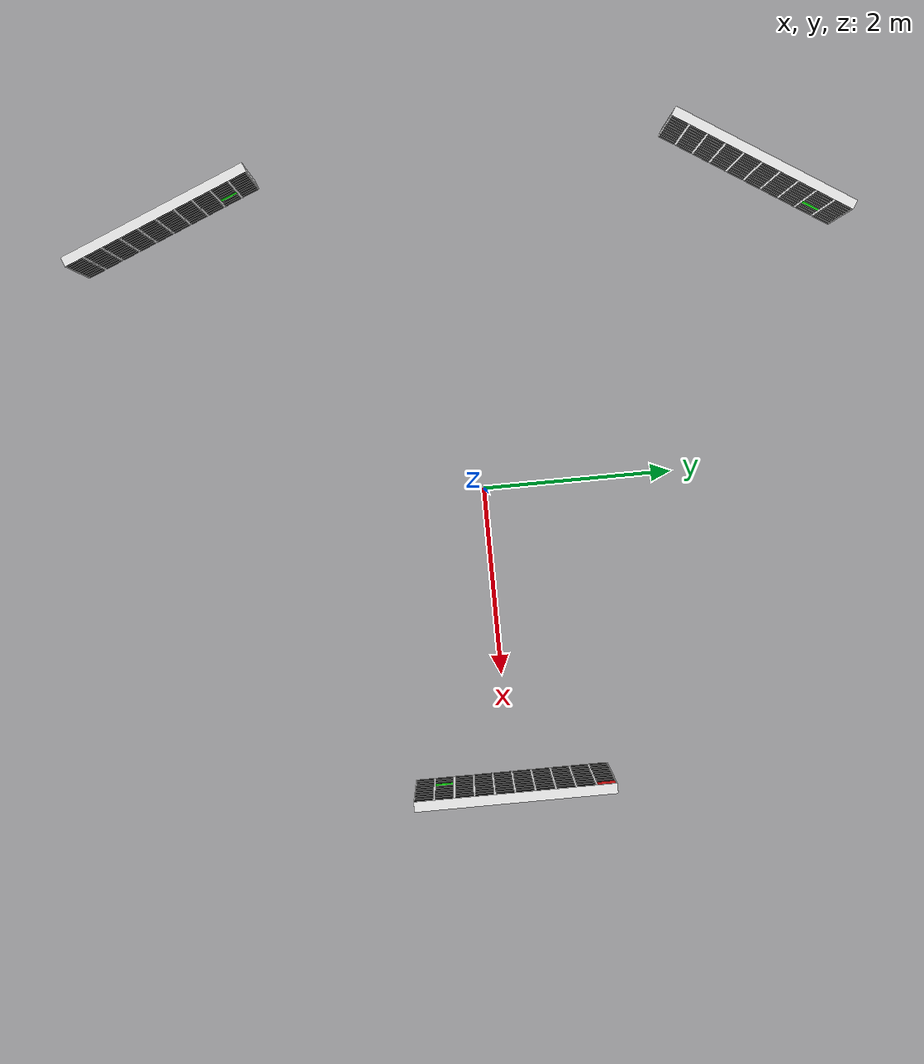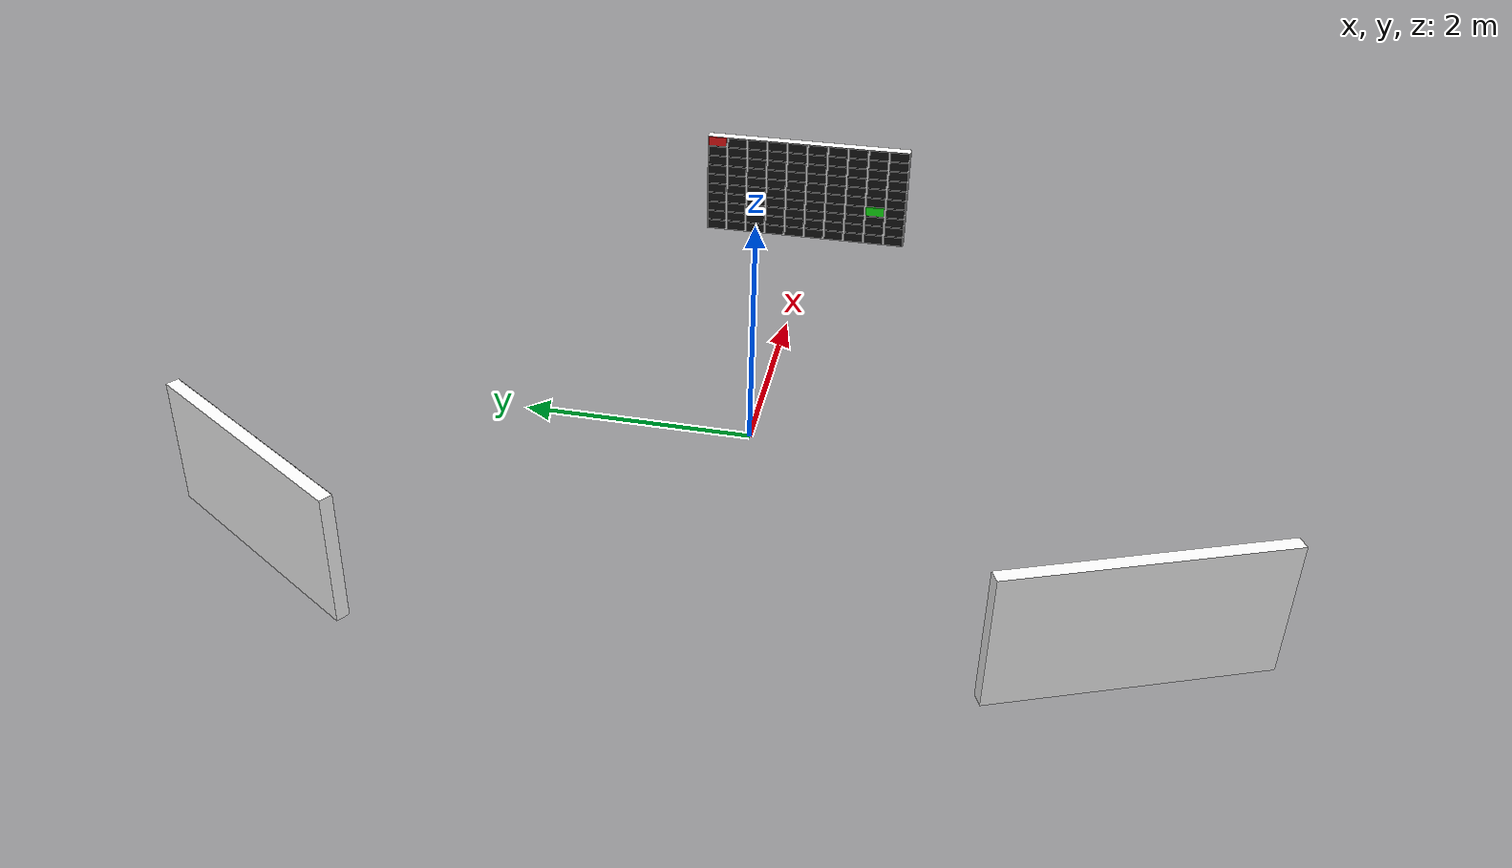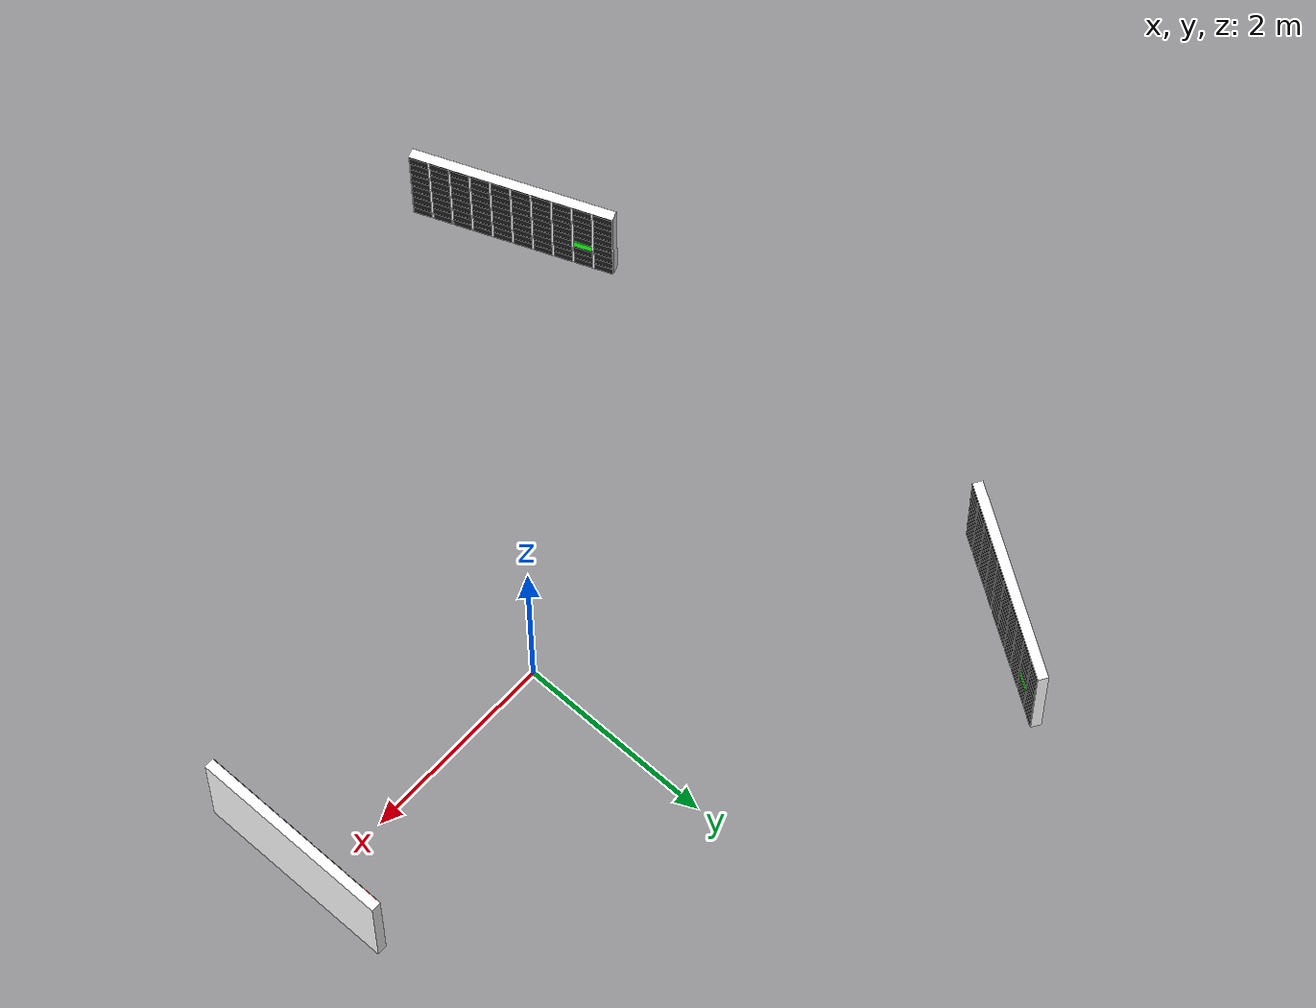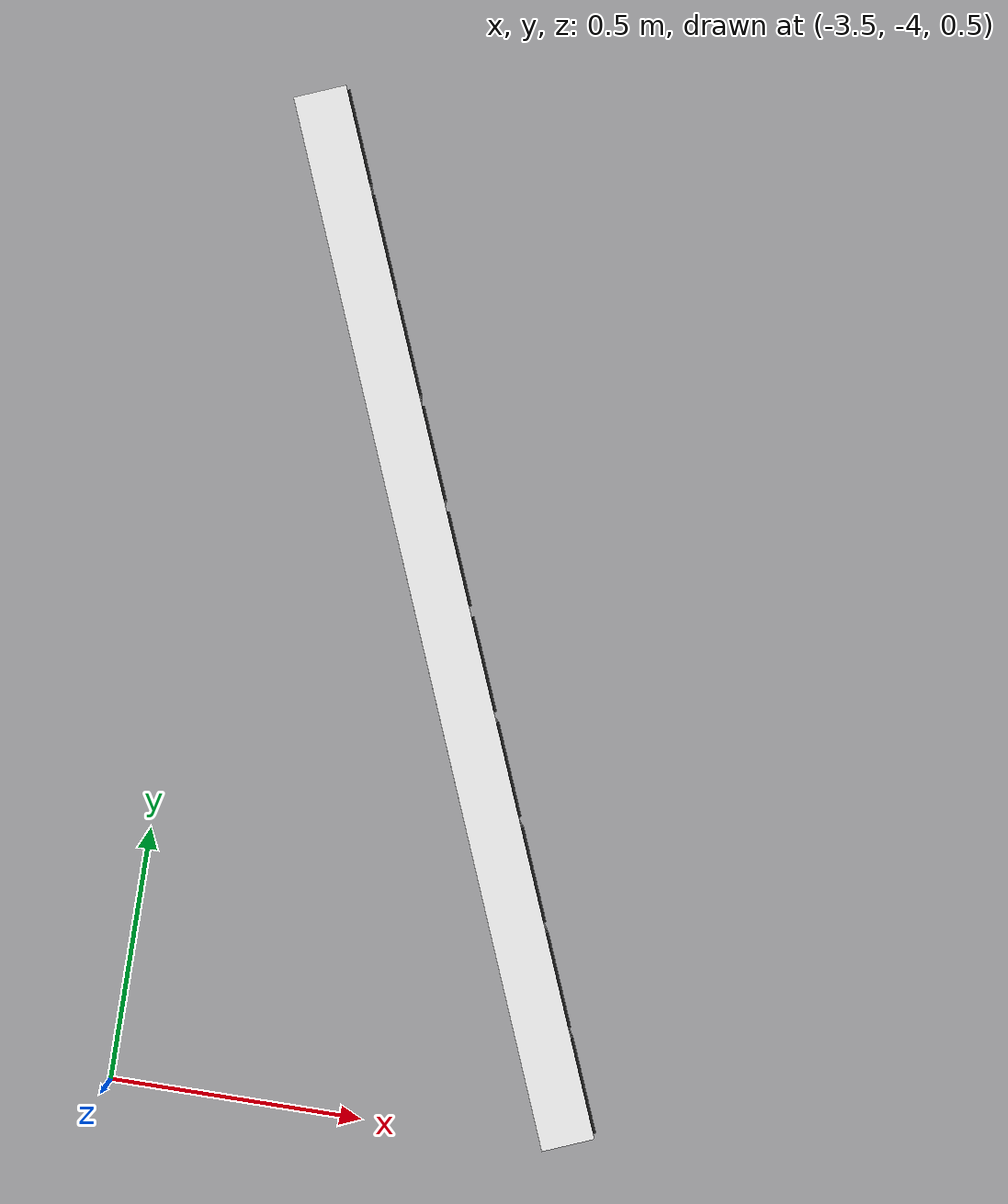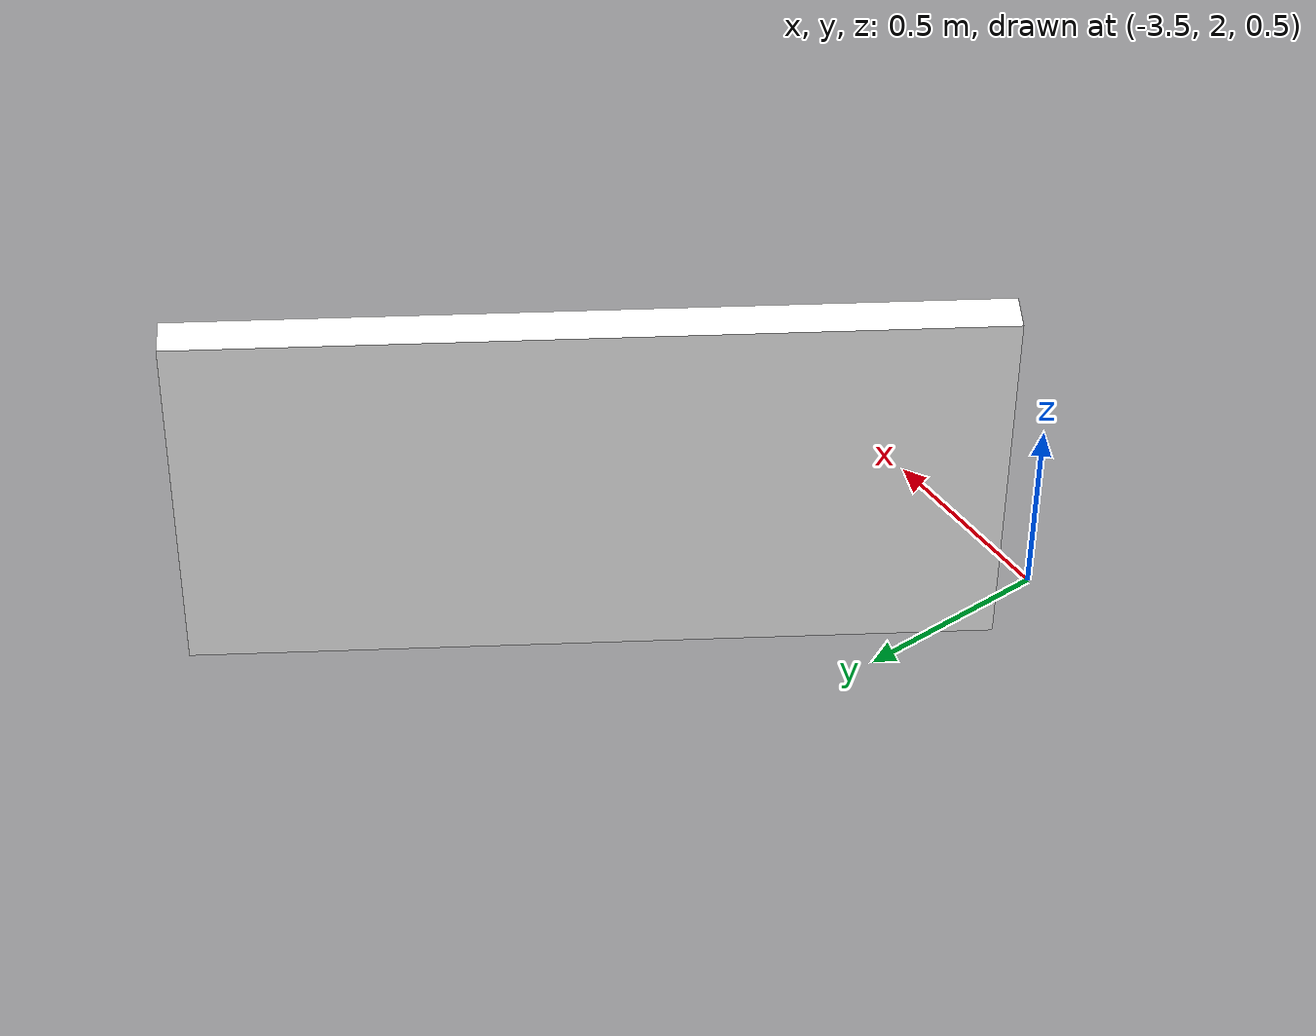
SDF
<sdf version="1.9">
 <world name="forest_with_panels">
  <plugin filename="gz-sim-physics-system" name="gz::sim::systems::Physics"/>
  <plugin filename="gz-sim-scene-broadcaster-system" name="gz::sim::systems::SceneBroadcaster"/>
  <plugin filename="gz-sim-user-commands-system" name="gz::sim::systems::UserCommands"/>
  <plugin filename="gz-sim-sensors-system" name="gz::sim::systems::Sensors"/>
  <light type="directional" name="sun">
   <pose>0 0 10 0 0 0</pose>
   <diffuse>0.8 0.8 0.8 1</diffuse>
   <specular>0.2 0.2 0.2 1</specular>
   <direction>-0.5 0.1 -0.9</direction>
  </light>
  <physics type="ode">
   <max_step_size>0.004</max_step_size>
   <real_time_factor>1.0</real_time_factor>
   <real_time_update_rate>250</real_time_update_rate>
  </physics>
  <gravity>0 0 -9.8</gravity>
  <magnetic_field>6e-06 2.3e-05 -4.2e-05</magnetic_field>
  <atmosphere type="adiabatic"/>
  <scene>
   <grid>false</grid>
   <ambient>0.4 0.4 0.4 1</ambient>
   <background>0.7 0.7 0.7 1</background>
   <shadows>true</shadows>
  </scene>
  <model name="panel_1">
   <pose>3 0 1 0 -1.57 0</pose>
   <static>true</static>
   <link name="panel_outline">
    <visual name="panel_outline_visual">
     <geometry><box><size>1.0 2.0 0.1</size></box></geometry>
     <material>
      <ambient>1.0 1.0 1.0 1</ambient>
      <diffuse>1.0 1.0 1.0 1</diffuse>
      <specular>1.0 1.0 1.0 1</specular>
      <emissive>0 0 0 0</emissive>
     </material>
    </visual>
   </link>
   <link name="block_1_1">
    <visual name="block_1_1_visual">
     <pose>0.45 0.9 0.05 0 0 0</pose>
     <geometry><box><size>0.09 0.18 0.01</size></box></geometry>
     <material>
      <ambient>0.0 0.0 0.0 1</ambient>
      <diffuse>1.0 0.1 0.1 1</diffuse>
      <specular>0.1 0.1 0.1 1</specular>
      <emissive>0 0 0 0</emissive>
     </material>
    </visual>
   </link>
   <link name="block_2_1">
    <visual name="block_2_1_visual">
     <pose>0.35 0.9 0.05 0 0 0</pose>
     <geometry><box><size>0.09 0.18 0.01</size></box></geometry>
     <material>
      <ambient>0.0 0.0 0.0 1</ambient>
      <diffuse>0.1 0.1 0.1 1</diffuse>
      <specular>0.1 0.1 0.1 1</specular>
      <emissive>0 0 0 0</emissive>
     </material>
    </visual>
   </link>
   <link name="block_3_1">
    <visual name="block_3_1_visual">
     <pose>0.25 0.9 0.05 0 0 0</pose>
     <geometry><box><size>0.09 0.18 0.01</size></box></geometry>
     <material>
      <ambient>0.0 0.0 0.0 1</ambient>
      <diffuse>0.1 0.1 0.1 1</diffuse>
      <specular>0.1 0.1 0.1 1</specular>
      <emissive>0 0 0 0</emissive>
     </material>
    </visual>
   </link>
   <link name="block_4_1">
    <visual name="block_4_1_visual">
     <pose>0.15 0.9 0.05 0 0 0</pose>
     <geometry><box><size>0.09 0.18 0.01</size></box></geometry>
     <material>
      <ambient>0.0 0.0 0.0 1</ambient>
      <diffuse>0.1 0.1 0.1 1</diffuse>
      <specular>0.1 0.1 0.1 1</specular>
      <emissive>0 0 0 0</emissive>
     </material>
    </visual>
   </link>
   <link name="block_5_1">
    <visual name="block_5_1_visual">
     <pose>0.05 0.9 0.05 0 0 0</pose>
     <geometry><box><size>0.09 0.18 0.01</size></box></geometry>
     <material>
      <ambient>0.0 0.0 0.0 1</ambient>
      <diffuse>0.1 0.1 0.1 1</diffuse>
      <specular>0.1 0.1 0.1 1</specular>
      <emissive>0 0 0 0</emissive>
     </material>
    </visual>
   </link>
   <link name="block_6_1">
    <visual name="block_6_1_visual">
     <pose>-0.05 0.9 0.05 0 0 0</pose>
     <geometry><box><size>0.09 0.18 0.01</size></box></geometry>
     <material>
      <ambient>0.0 0.0 0.0 1</ambient>
      <diffuse>0.1 0.1 0.1 1</diffuse>
      <specular>0.1 0.1 0.1 1</specular>
      <emissive>0 0 0 0</emissive>
     </material>
    </visual>
   </link>
   <link name="block_7_1">
    <visual name="block_7_1_visual">
     <pose>-0.15 0.9 0.05 0 0 0</pose>
     <geometry><box><size>0.09 0.18 0.01</size></box></geometry>
     <material>
      <ambient>0.0 0.0 0.0 1</ambient>
      <diffuse>0.1 0.1 0.1 1</diffuse>
      <specular>0.1 0.1 0.1 1</specular>
      <emissive>0 0 0 0</emissive>
     </material>
    </visual>
   </link>
   <link name="block_8_1">
    <visual name="block_8_1_visual">
     <pose>-0.25 0.9 0.05 0 0 0</pose>
     <geometry><box><size>0.09 0.18 0.01</size></box></geometry>
     <material>
      <ambient>0.0 0.0 0.0 1</ambient>
      <diffuse>0.1 0.1 0.1 1</diffuse>
      <specular>0.1 0.1 0.1 1</specular>
      <emissive>0 0 0 0</emissive>
     </material>
    </visual>
   </link>
   <link name="block_9_1">
    <visual name="block_9_1_visual">
     <pose>-0.35 0.9 0.05 0 0 0</pose>
     <geometry><box><size>0.09 0.18 0.01</size></box></geometry>
     <material>
      <ambient>0.0 0.0 0.0 1</ambient>
      <diffuse>0.1 0.1 0.1 1</diffuse>
      <specular>0.1 0.1 0.1 1</specular>
      <emissive>0 0 0 0</emissive>
     </material>
    </visual>
   </link>
   <link name="block_10_1">
    <visual name="block_10_1_visual">
     <pose>-0.45 0.9 0.05 0 0 0</pose>
     <geometry><box><size>0.09 0.18 0.01</size></box></geometry>
     <material>
      <ambient>0.0 0.0 0.0 1</ambient>
      <diffuse>0.1 0.1 0.1 1</diffuse>
      <specular>0.1 0.1 0.1 1</specular>
      <emissive>0 0 0 0</emissive>
     </material>
    </visual>
   </link>
   <link name="block_1_2">
    <visual name="block_1_2_visual">
     <pose>0.45 0.7 0.05 0 0 0</pose>
     <geometry><box><size>0.09 0.18 0.01</size></box></geometry>
     <material>
      <ambient>0.0 0.0 0.0 1</ambient>
      <diffuse>0.1 0.1 0.1 1</diffuse>
      <specular>0.1 0.1 0.1 1</specular>
      <emissive>0 0 0 0</emissive>
     </material>
    </visual>
   </link>
   <link name="block_2_2">
    <visual name="block_2_2_visual">
     <pose>0.35 0.7 0.05 0 0 0</pose>
     <geometry><box><size>0.09 0.18 0.01</size></box></geometry>
     <material>
      <ambient>0.0 0.0 0.0 1</ambient>
      <diffuse>0.1 0.1 0.1 1</diffuse>
      <specular>0.1 0.1 0.1 1</specular>
      <emissive>0 0 0 0</emissive>
     </material>
    </visual>
   </link>
   <link name="block_3_2">
    <visual name="block_3_2_visual">
     <pose>0.25 0.7 0.05 0 0 0</pose>
     <geometry><box><size>0.09 0.18 0.01</size></box></geometry>
     <material>
      <ambient>0.0 0.0 0.0 1</ambient>
      <diffuse>0.1 0.1 0.1 1</diffuse>
      <specular>0.1 0.1 0.1 1</specular>
      <emissive>0 0 0 0</emissive>
     </material>
    </visual>
   </link>
   <link name="block_4_2">
    <visual name="block_4_2_visual">
     <pose>0.15 0.7 0.05 0 0 0</pose>
     <geometry><box><size>0.09 0.18 0.01</size></box></geometry>
     <material>
      <ambient>0.0 0.0 0.0 1</ambient>
      <diffuse>0.1 0.1 0.1 1</diffuse>
      <specular>0.1 0.1 0.1 1</specular>
      <emissive>0 0 0 0</emissive>
     </material>
    </visual>
   </link>
   <link name="block_5_2">
    <visual name="block_5_2_visual">
     <pose>0.05 0.7 0.05 0 0 0</pose>
     <geometry><box><size>0.09 0.18 0.01</size></box></geometry>
     <material>
      <ambient>0.0 0.0 0.0 1</ambient>
      <diffuse>0.1 0.1 0.1 1</diffuse>
      <specular>0.1 0.1 0.1 1</specular>
      <emissive>0 0 0 0</emissive>
     </material>
    </visual>
   </link>
   <link name="block_6_2">
    <visual name="block_6_2_visual">
     <pose>-0.05 0.7 0.05 0 0 0</pose>
     <geometry><box><size>0.09 0.18 0.01</size></box></geometry>
     <material>
      <ambient>0.0 0.0 0.0 1</ambient>
      <diffuse>0.1 0.1 0.1 1</diffuse>
      <specular>0.1 0.1 0.1 1</specular>
      <emissive>0 0 0 0</emissive>
     </material>
    </visual>
   </link>
   <link name="block_7_2">
    <visual name="block_7_2_visual">
     <pose>-0.15 0.7 0.05 0 0 0</pose>
     <geometry><box><size>0.09 0.18 0.01</size></box></geometry>
     <material>
      <ambient>0.0 0.0 0.0 1</ambient>
      <diffuse>0.1 0.1 0.1 1</diffuse>
      <specular>0.1 0.1 0.1 1</specular>
      <emissive>0 0 0 0</emissive>
     </material>
    </visual>
   </link>
   <link name="block_8_2">
    <visual name="block_8_2_visual">
     <pose>-0.25 0.7 0.05 0 0 0</pose>
     <geometry><box><size>0.09 0.18 0.01</size></box></geometry>
     <material>
      <ambient>0.0 0.0 0.0 1</ambient>
      <diffuse>0.1 0.1 0.1 1</diffuse>
      <specular>0.1 0.1 0.1 1</specular>
      <emissive>0 0 0 0</emissive>
     </material>
    </visual>
   </link>
   <link name="block_9_2">
    <visual name="block_9_2_visual">
     <pose>-0.35 0.7 0.05 0 0 0</pose>
     <geometry><box><size>0.09 0.18 0.01</size></box></geometry>
     <material>
      <ambient>0.0 0.0 0.0 1</ambient>
      <diffuse>0.1 0.1 0.1 1</diffuse>
      <specular>0.1 0.1 0.1 1</specular>
      <emissive>0 0 0 0</emissive>
     </material>
    </visual>
   </link>
   <link name="block_10_2">
    <visual name="block_10_2_visual">
     <pose>-0.45 0.7 0.05 0 0 0</pose>
     <geometry><box><size>0.09 0.18 0.01</size></box></geometry>
     <material>
      <ambient>0.0 0.0 0.0 1</ambient>
      <diffuse>0.1 0.1 0.1 1</diffuse>
      <specular>0.1 0.1 0.1 1</specular>
      <emissive>0 0 0 0</emissive>
     </material>
    </visual>
   </link>
   <link name="block_1_3">
    <visual name="block_1_3_visual">
     <pose>0.45 0.5 0.05 0 0 0</pose>
     <geometry><box><size>0.09 0.18 0.01</size></box></geometry>
     <material>
      <ambient>0.0 0.0 0.0 1</ambient>
      <diffuse>0.1 0.1 0.1 1</diffuse>
      <specular>0.1 0.1 0.1 1</specular>
      <emissive>0 0 0 0</emissive>
     </material>
    </visual>
   </link>
   <link name="block_2_3">
    <visual name="block_2_3_visual">
     <pose>0.35 0.5 0.05 0 0 0</pose>
     <geometry><box><size>0.09 0.18 0.01</size></box></geometry>
     <material>
      <ambient>0.0 0.0 0.0 1</ambient>
      <diffuse>0.1 0.1 0.1 1</diffuse>
      <specular>0.1 0.1 0.1 1</specular>
      <emissive>0 0 0 0</emissive>
     </material>
    </visual>
   </link>
   <link name="block_3_3">
    <visual name="block_3_3_visual">
     <pose>0.25 0.5 0.05 0 0 0</pose>
     <geometry><box><size>0.09 0.18 0.01</size></box></geometry>
     <material>
      <ambient>0.0 0.0 0.0 1</ambient>
      <diffuse>0.1 0.1 0.1 1</diffuse>
      <specular>0.1 0.1 0.1 1</specular>
      <emissive>0 0 0 0</emissive>
     </material>
    </visual>
   </link>
   <link name="block_4_3">
    <visual name="block_4_3_visual">
     <pose>0.15 0.5 0.05 0 0 0</pose>
     <geometry><box><size>0.09 0.18 0.01</size></box></geometry>
     <material>
      <ambient>0.0 0.0 0.0 1</ambient>
      <diffuse>0.1 0.1 0.1 1</diffuse>
      <specular>0.1 0.1 0.1 1</specular>
      <emissive>0 0 0 0</emissive>
     </material>
    </visual>
   </link>
   <link name="block_5_3">
    <visual name="block_5_3_visual">
     <pose>0.05 0.5 0.05 0 0 0</pose>
     <geometry><box><size>0.09 0.18 0.01</size></box></geometry>
     <material>
      <ambient>0.0 0.0 0.0 1</ambient>
      <diffuse>0.1 0.1 0.1 1</diffuse>
      <specular>0.1 0.1 0.1 1</specular>
      <emissive>0 0 0 0</emissive>
     </material>
    </visual>
   </link>
   <link name="block_6_3">
    <visual name="block_6_3_visual">
     <pose>-0.05 0.5 0.05 0 0 0</pose>
     <geometry><box><size>0.09 0.18 0.01</size></box></geometry>
     <material>
      <ambient>0.0 0.0 0.0 1</ambient>
      <diffuse>0.1 0.1 0.1 1</diffuse>
      <specular>0.1 0.1 0.1 1</specular>
      <emissive>0 0 0 0</emissive>
     </material>
    </visual>
   </link>
   <link name="block_7_3">
    <visual name="block_7_3_visual">
     <pose>-0.15 0.5 0.05 0 0 0</pose>
     <geometry><box><size>0.09 0.18 0.01</size></box></geometry>
     <material>
      <ambient>0.0 0.0 0.0 1</ambient>
      <diffuse>0.1 0.1 0.1 1</diffuse>
      <specular>0.1 0.1 0.1 1</specular>
      <emissive>0 0 0 0</emissive>
     </material>
    </visual>
   </link>
   <link name="block_8_3">
    <visual name="block_8_3_visual">
     <pose>-0.25 0.5 0.05 0 0 0</pose>
     <geometry><box><size>0.09 0.18 0.01</size></box></geometry>
     <material>
      <ambient>0.0 0.0 0.0 1</ambient>
      <diffuse>0.1 0.1 0.1 1</diffuse>
      <specular>0.1 0.1 0.1 1</specular>
      <emissive>0 0 0 0</emissive>
     </material>
    </visual>
   </link>
   <link name="block_9_3">
    <visual name="block_9_3_visual">
     <pose>-0.35 0.5 0.05 0 0 0</pose>
     <geometry><box><size>0.09 0.18 0.01</size></box></geometry>
     <material>
      <ambient>0.0 0.0 0.0 1</ambient>
      <diffuse>0.1 0.1 0.1 1</diffuse>
      <specular>0.1 0.1 0.1 1</specular>
      <emissive>0 0 0 0</emissive>
     </material>
    </visual>
   </link>
   <link name="block_10_3">
    <visual name="block_10_3_visual">
     <pose>-0.45 0.5 0.05 0 0 0</pose>
     <geometry><box><size>0.09 0.18 0.01</size></box></geometry>
     <material>
      <ambient>0.0 0.0 0.0 1</ambient>
      <diffuse>0.1 0.1 0.1 1</diffuse>
      <specular>0.1 0.1 0.1 1</specular>
      <emissive>0 0 0 0</emissive>
     </material>
    </visual>
   </link>
   <link name="block_1_4">
    <visual name="block_1_4_visual">
     <pose>0.45 0.3 0.05 0 0 0</pose>
     <geometry><box><size>0.09 0.18 0.01</size></box></geometry>
     <material>
      <ambient>0.0 0.0 0.0 1</ambient>
      <diffuse>0.1 0.1 0.1 1</diffuse>
      <specular>0.1 0.1 0.1 1</specular>
      <emissive>0 0 0 0</emissive>
     </material>
    </visual>
   </link>
   <link name="block_2_4">
    <visual name="block_2_4_visual">
     <pose>0.35 0.3 0.05 0 0 0</pose>
     <geometry><box><size>0.09 0.18 0.01</size></box></geometry>
     <material>
      <ambient>0.0 0.0 0.0 1</ambient>
      <diffuse>0.1 0.1 0.1 1</diffuse>
      <specular>0.1 0.1 0.1 1</specular>
      <emissive>0 0 0 0</emissive>
     </material>
    </visual>
   </link>
   <link name="block_3_4">
    <visual name="block_3_4_visual">
     <pose>0.25 0.3 0.05 0 0 0</pose>
     <geometry><box><size>0.09 0.18 0.01</size></box></geometry>
     <material>
      <ambient>0.0 0.0 0.0 1</ambient>
      <diffuse>0.1 0.1 0.1 1</diffuse>
      <specular>0.1 0.1 0.1 1</specular>
      <emissive>0 0 0 0</emissive>
     </material>
    </visual>
   </link>
   <link name="block_4_4">
    <visual name="block_4_4_visual">
     <pose>0.15 0.3 0.05 0 0 0</pose>
     <geometry><box><size>0.09 0.18 0.01</size></box></geometry>
     <material>
      <ambient>0.0 0.0 0.0 1</ambient>
      <diffuse>0.1 0.1 0.1 1</diffuse>
      <specular>0.1 0.1 0.1 1</specular>
      <emissive>0 0 0 0</emissive>
     </material>
    </visual>
   </link>
   <link name="block_5_4">
    <visual name="block_5_4_visual">
     <pose>0.05 0.3 0.05 0 0 0</pose>
     <geometry><box><size>0.09 0.18 0.01</size></box></geometry>
     <material>
      <ambient>0.0 0.0 0.0 1</ambient>
      <diffuse>0.1 0.1 0.1 1</diffuse>
      <specular>0.1 0.1 0.1 1</specular>
      <emissive>0 0 0 0</emissive>
     </material>
    </visual>
   </link>
   <link name="block_6_4">
    <visual name="block_6_4_visual">
     <pose>-0.05 0.3 0.05 0 0 0</pose>
     <geometry><box><size>0.09 0.18 0.01</size></box></geometry>
     <material>
      <ambient>0.0 0.0 0.0 1</ambient>
      <diffuse>0.1 0.1 0.1 1</diffuse>
      <specular>0.1 0.1 0.1 1</specular>
      <emissive>0 0 0 0</emissive>
     </material>
    </visual>
   </link>
   <link name="block_7_4">
    <visual name="block_7_4_visual">
     <pose>-0.15 0.3 0.05 0 0 0</pose>
     <geometry><box><size>0.09 0.18 0.01</size></box></geometry>
     <material>
      <ambient>0.0 0.0 0.0 1</ambient>
      <diffuse>0.1 0.1 0.1 1</diffuse>
      <specular>0.1 0.1 0.1 1</specular>
      <emissive>0 0 0 0</emissive>
     </material>
    </visual>
   </link>
   <link name="block_8_4">
    <visual name="block_8_4_visual">
     <pose>-0.25 0.3 0.05 0 0 0</pose>
     <geometry><box><size>0.09 0.18 0.01</size></box></geometry>
     <material>
      <ambient>0.0 0.0 0.0 1</ambient>
      <diffuse>0.1 0.1 0.1 1</diffuse>
      <specular>0.1 0.1 0.1 1</specular>
      <emissive>0 0 0 0</emissive>
     </material>
    </visual>
   </link>
   <link name="block_9_4">
    <visual name="block_9_4_visual">
     <pose>-0.35 0.3 0.05 0 0 0</pose>
     <geometry><box><size>0.09 0.18 0.01</size></box></geometry>
     <material>
      <ambient>0.0 0.0 0.0 1</ambient>
      <diffuse>0.1 0.1 0.1 1</diffuse>
      <specular>0.1 0.1 0.1 1</specular>
      <emissive>0 0 0 0</emissive>
     </material>
    </visual>
   </link>
   <link name="block_10_4">
    <visual name="block_10_2_visual">
     <pose>-0.45 0.3 0.05 0 0 0</pose>
     <geometry><box><size>0.09 0.18 0.01</size></box></geometry>
     <material>
      <ambient>0.0 0.0 0.0 1</ambient>
      <diffuse>0.1 0.1 0.1 1</diffuse>
      <specular>0.1 0.1 0.1 1</specular>
      <emissive>0 0 0 0</emissive>
     </material>
    </visual>
   </link>
   <link name="block_1_5">
    <visual name="block_1_5_visual">
     <pose>0.45 0.1 0.05 0 0 0</pose>
     <geometry><box><size>0.09 0.18 0.01</size></box></geometry>
     <material>
      <ambient>0.0 0.0 0.0 1</ambient>
      <diffuse>0.1 0.1 0.1 1</diffuse>
      <specular>0.1 0.1 0.1 1</specular>
      <emissive>0 0 0 0</emissive>
     </material>
    </visual>
   </link>
   <link name="block_2_5">
    <visual name="block_2_5_visual">
     <pose>0.35 0.1 0.05 0 0 0</pose>
     <geometry><box><size>0.09 0.18 0.01</size></box></geometry>
     <material>
      <ambient>0.0 0.0 0.0 1</ambient>
      <diffuse>0.1 0.1 0.1 1</diffuse>
      <specular>0.1 0.1 0.1 1</specular>
      <emissive>0 0 0 0</emissive>
     </material>
    </visual>
   </link>
   <link name="block_3_5">
    <visual name="block_3_5_visual">
     <pose>0.25 0.1 0.05 0 0 0</pose>
     <geometry><box><size>0.09 0.18 0.01</size></box></geometry>
     <material>
      <ambient>0.0 0.0 0.0 1</ambient>
      <diffuse>0.1 0.1 0.1 1</diffuse>
      <specular>0.1 0.1 0.1 1</specular>
      <emissive>0 0 0 0</emissive>
     </material>
    </visual>
   </link>
   <link name="block_4_5">
    <visual name="block_4_5_visual">
     <pose>0.15 0.1 0.05 0 0 0</pose>
     <geometry><box><size>0.09 0.18 0.01</size></box></geometry>
     <material>
      <ambient>0.0 0.0 0.0 1</ambient>
      <diffuse>0.1 0.1 0.1 1</diffuse>
      <specular>0.1 0.1 0.1 1</specular>
      <emissive>0 0 0 0</emissive>
     </material>
    </visual>
   </link>
   <link name="block_5_5">
    <visual name="block_5_5_visual">
     <pose>0.05 0.1 0.05 0 0 0</pose>
     <geometry><box><size>0.09 0.18 0.01</size></box></geometry>
     <material>
      <ambient>0.0 0.0 0.0 1</ambient>
      <diffuse>0.1 0.1 0.1 1</diffuse>
      <specular>0.1 0.1 0.1 1</specular>
      <emissive>0 0 0 0</emissive>
     </material>
    </visual>
   </link>
   <link name="block_6_5">
    <visual name="block_6_5_visual">
     <pose>-0.05 0.1 0.05 0 0 0</pose>
     <geometry><box><size>0.09 0.18 0.01</size></box></geometry>
     <material>
      <ambient>0.0 0.0 0.0 1</ambient>
      <diffuse>0.1 0.1 0.1 1</diffuse>
      <specular>0.1 0.1 0.1 1</specular>
      <emissive>0 0 0 0</emissive>
     </material>
    </visual>
   </link>
   <link name="block_7_5">
    <visual name="block_7_5_visual">
     <pose>-0.15 0.1 0.05 0 0 0</pose>
     <geometry><box><size>0.09 0.18 0.01</size></box></geometry>
     <material>
      <ambient>0.0 0.0 0.0 1</ambient>
      <diffuse>0.1 0.1 0.1 1</diffuse>
      <specular>0.1 0.1 0.1 1</specular>
      <emissive>0 0 0 0</emissive>
     </material>
    </visual>
   </link>
   <link name="block_8_5">
    <visual name="block_8_5_visual">
     <pose>-0.25 0.1 0.05 0 0 0</pose>
     <geometry><box><size>0.09 0.18 0.01</size></box></geometry>
     <material>
      <ambient>0.0 0.0 0.0 1</ambient>
      <diffuse>0.1 0.1 0.1 1</diffuse>
      <specular>0.1 0.1 0.1 1</specular>
      <emissive>0 0 0 0</emissive>
     </material>
    </visual>
   </link>
   <link name="block_9_5">
    <visual name="block_9_5_visual">
     <pose>-0.35 0.1 0.05 0 0 0</pose>
     <geometry><box><size>0.09 0.18 0.01</size></box></geometry>
     <material>
      <ambient>0.0 0.0 0.0 1</ambient>
      <diffuse>0.1 0.1 0.1 1</diffuse>
      <specular>0.1 0.1 0.1 1</specular>
      <emissive>0 0 0 0</emissive>
     </material>
    </visual>
   </link>
   <link name="block_10_5">
    <visual name="block_10_5_visual">
     <pose>-0.45 0.1 0.05 0 0 0</pose>
     <geometry><box><size>0.09 0.18 0.01</size></box></geometry>
     <material>
      <ambient>0.0 0.0 0.0 1</ambient>
      <diffuse>0.1 0.1 0.1 1</diffuse>
      <specular>0.1 0.1 0.1 1</specular>
      <emissive>0 0 0 0</emissive>
     </material>
    </visual>
   </link>
   <link name="block_1_6">
    <visual name="block_1_6_visual">
     <pose>0.45 -0.1 0.05 0 0 0</pose>
     <geometry><box><size>0.09 0.18 0.01</size></box></geometry>
     <material>
      <ambient>0.0 0.0 0.0 1</ambient>
      <diffuse>0.1 0.1 0.1 1</diffuse>
      <specular>0.1 0.1 0.1 1</specular>
      <emissive>0 0 0 0</emissive>
     </material>
    </visual>
   </link>
   <link name="block_2_6">
    <visual name="block_2_6_visual">
     <pose>0.35 -0.1 0.05 0 0 0</pose>
     <geometry><box><size>0.09 0.18 0.01</size></box></geometry>
     <material>
      <ambient>0.0 0.0 0.0 1</ambient>
      <diffuse>0.1 0.1 0.1 1</diffuse>
      <specular>0.1 0.1 0.1 1</specular>
      <emissive>0 0 0 0</emissive>
     </material>
    </visual>
   </link>
   <link name="block_3_6">
    <visual name="block_3_6_visual">
     <pose>0.25 -0.1 0.05 0 0 0</pose>
     <geometry><box><size>0.09 0.18 0.01</size></box></geometry>
     <material>
      <ambient>0.0 0.0 0.0 1</ambient>
      <diffuse>0.1 0.1 0.1 1</diffuse>
      <specular>0.1 0.1 0.1 1</specular>
      <emissive>0 0 0 0</emissive>
     </material>
    </visual>
   </link>
   <link name="block_4_6">
    <visual name="block_4_6_visual">
     <pose>0.15 -0.1 0.05 0 0 0</pose>
     <geometry><box><size>0.09 0.18 0.01</size></box></geometry>
     <material>
      <ambient>0.0 0.0 0.0 1</ambient>
      <diffuse>0.1 0.1 0.1 1</diffuse>
      <specular>0.1 0.1 0.1 1</specular>
      <emissive>0 0 0 0</emissive>
     </material>
    </visual>
   </link>
   <link name="block_5_6">
    <visual name="block_5_6_visual">
     <pose>0.05 -0.1 0.05 0 0 0</pose>
     <geometry><box><size>0.09 0.18 0.01</size></box></geometry>
     <material>
      <ambient>0.0 0.0 0.0 1</ambient>
      <diffuse>0.1 0.1 0.1 1</diffuse>
      <specular>0.1 0.1 0.1 1</specular>
      <emissive>0 0 0 0</emissive>
     </material>
    </visual>
   </link>
   <link name="block_6_6">
    <visual name="block_6_6_visual">
     <pose>-0.05 -0.1 0.05 0 0 0</pose>
     <geometry><box><size>0.09 0.18 0.01</size></box></geometry>
     <material>
      <ambient>0.0 0.0 0.0 1</ambient>
      <diffuse>0.1 0.1 0.1 1</diffuse>
      <specular>0.1 0.1 0.1 1</specular>
      <emissive>0 0 0 0</emissive>
     </material>
    </visual>
   </link>
   <link name="block_7_6">
    <visual name="block_7_6_visual">
     <pose>-0.15 -0.1 0.05 0 0 0</pose>
     <geometry><box><size>0.09 0.18 0.01</size></box></geometry>
     <material>
      <ambient>0.0 0.0 0.0 1</ambient>
      <diffuse>0.1 0.1 0.1 1</diffuse>
      <specular>0.1 0.1 0.1 1</specular>
      <emissive>0 0 0 0</emissive>
     </material>
    </visual>
   </link>
   <link name="block_8_6">
    <visual name="block_8_2_visual">
     <pose>-0.25 -0.1 0.05 0 0 0</pose>
     <geometry><box><size>0.09 0.18 0.01</size></box></geometry>
     <material>
      <ambient>0.0 0.0 0.0 1</ambient>
      <diffuse>0.1 0.1 0.1 1</diffuse>
      <specular>0.1 0.1 0.1 1</specular>
      <emissive>0 0 0 0</emissive>
     </material>
    </visual>
   </link>
   <link name="block_9_6">
    <visual name="block_9_2_visual">
     <pose>-0.35 -0.1 0.05 0 0 0</pose>
     <geometry><box><size>0.09 0.18 0.01</size></box></geometry>
     <material>
      <ambient>0.0 0.0 0.0 1</ambient>
      <diffuse>0.1 0.1 0.1 1</diffuse>
      <specular>0.1 0.1 0.1 1</specular>
      <emissive>0 0 0 0</emissive>
     </material>
    </visual>
   </link>
   <link name="block_10_6">
    <visual name="block_10_6_visual">
     <pose>-0.45 -0.1 0.05 0 0 0</pose>
     <geometry><box><size>0.09 0.18 0.01</size></box></geometry>
     <material>
      <ambient>0.0 0.0 0.0 1</ambient>
      <diffuse>0.1 0.1 0.1 1</diffuse>
      <specular>0.1 0.1 0.1 1</specular>
      <emissive>0 0 0 0</emissive>
     </material>
    </visual>
   </link>
   <link name="block_1_7">
    <visual name="block_1_7_visual">
     <pose>0.45 -0.3 0.05 0 0 0</pose>
     <geometry><box><size>0.09 0.18 0.01</size></box></geometry>
     <material>
      <ambient>0.0 0.0 0.0 1</ambient>
      <diffuse>0.1 0.1 0.1 1</diffuse>
      <specular>0.1 0.1 0.1 1</specular>
      <emissive>0 0 0 0</emissive>
     </material>
    </visual>
   </link>
   <link name="block_2_7">
    <visual name="block_2_7_visual">
     <pose>0.35 -0.3 0.05 0 0 0</pose>
     <geometry><box><size>0.09 0.18 0.01</size></box></geometry>
     <material>
      <ambient>0.0 0.0 0.0 1</ambient>
      <diffuse>0.1 0.1 0.1 1</diffuse>
      <specular>0.1 0.1 0.1 1</specular>
      <emissive>0 0 0 0</emissive>
     </material>
    </visual>
   </link>
   <link name="block_3_7">
    <visual name="block_3_7_visual">
     <pose>0.25 -0.3 0.05 0 0 0</pose>
     <geometry><box><size>0.09 0.18 0.01</size></box></geometry>
     <material>
      <ambient>0.0 0.0 0.0 1</ambient>
      <diffuse>0.1 0.1 0.1 1</diffuse>
      <specular>0.1 0.1 0.1 1</specular>
      <emissive>0 0 0 0</emissive>
     </material>
    </visual>
   </link>
   <link name="block_4_7">
    <visual name="block_4_7_visual">
     <pose>0.15 -0.3 0.05 0 0 0</pose>
     <geometry><box><size>0.09 0.18 0.01</size></box></geometry>
     <material>
      <ambient>0.0 0.0 0.0 1</ambient>
      <diffuse>0.1 0.1 0.1 1</diffuse>
      <specular>0.1 0.1 0.1 1</specular>
      <emissive>0 0 0 0</emissive>
     </material>
    </visual>
   </link>
   <link name="block_5_7">
    <visual name="block_5_7_visual">
     <pose>0.05 -0.3 0.05 0 0 0</pose>
     <geometry><box><size>0.09 0.18 0.01</size></box></geometry>
     <material>
      <ambient>0.0 0.0 0.0 1</ambient>
      <diffuse>0.1 0.1 0.1 1</diffuse>
      <specular>0.1 0.1 0.1 1</specular>
      <emissive>0 0 0 0</emissive>
     </material>
    </visual>
   </link>
   <link name="block_6_7">
    <visual name="block_6_7_visual">
     <pose>-0.05 -0.3 0.05 0 0 0</pose>
     <geometry><box><size>0.09 0.18 0.01</size></box></geometry>
     <material>
      <ambient>0.0 0.0 0.0 1</ambient>
      <diffuse>0.1 0.1 0.1 1</diffuse>
      <specular>0.1 0.1 0.1 1</specular>
      <emissive>0 0 0 0</emissive>
     </material>
    </visual>
   </link>
   <link name="block_7_7">
    <visual name="block_7_7_visual">
     <pose>-0.15 -0.3 0.05 0 0 0</pose>
     <geometry><box><size>0.09 0.18 0.01</size></box></geometry>
     <material>
      <ambient>0.0 0.0 0.0 1</ambient>
      <diffuse>0.1 0.1 0.1 1</diffuse>
      <specular>0.1 0.1 0.1 1</specular>
      <emissive>0 0 0 0</emissive>
     </material>
    </visual>
   </link>
   <link name="block_8_7">
    <visual name="block_8_7_visual">
     <pose>-0.25 -0.3 0.05 0 0 0</pose>
     <geometry><box><size>0.09 0.18 0.01</size></box></geometry>
     <material>
      <ambient>0.0 0.0 0.0 1</ambient>
      <diffuse>0.1 0.1 0.1 1</diffuse>
      <specular>0.1 0.1 0.1 1</specular>
      <emissive>0 0 0 0</emissive>
     </material>
    </visual>
   </link>
   <link name="block_9_7">
    <visual name="block_9_7_visual">
     <pose>-0.35 -0.3 0.05 0 0 0</pose>
     <geometry><box><size>0.09 0.18 0.01</size></box></geometry>
     <material>
      <ambient>0.0 0.0 0.0 1</ambient>
      <diffuse>0.1 0.1 0.1 1</diffuse>
      <specular>0.1 0.1 0.1 1</specular>
      <emissive>0 0 0 0</emissive>
     </material>
    </visual>
   </link>
   <link name="block_10_7">
    <visual name="block_10_7_visual">
     <pose>-0.45 -0.3 0.05 0 0 0</pose>
     <geometry><box><size>0.09 0.18 0.01</size></box></geometry>
     <material>
      <ambient>0.0 0.0 0.0 1</ambient>
      <diffuse>0.1 0.1 0.1 1</diffuse>
      <specular>0.1 0.1 0.1 1</specular>
      <emissive>0 0 0 0</emissive>
     </material>
    </visual>
   </link>
   <link name="block_1_8">
    <visual name="block_1_8_visual">
     <pose>0.45 -0.5 0.05 0 0 0</pose>
     <geometry><box><size>0.09 0.18 0.01</size></box></geometry>
     <material>
      <ambient>0.0 0.0 0.0 1</ambient>
      <diffuse>0.1 0.1 0.1 1</diffuse>
      <specular>0.1 0.1 0.1 1</specular>
      <emissive>0 0 0 0</emissive>
     </material>
    </visual>
   </link>
   <link name="block_2_8">
    <visual name="block_2_8_visual">
     <pose>0.35 -0.5 0.05 0 0 0</pose>
     <geometry><box><size>0.09 0.18 0.01</size></box></geometry>
     <material>
      <ambient>0.0 0.0 0.0 1</ambient>
      <diffuse>0.1 0.1 0.1 1</diffuse>
      <specular>0.1 0.1 0.1 1</specular>
      <emissive>0 0 0 0</emissive>
     </material>
    </visual>
   </link>
   <link name="block_3_8">
    <visual name="block_3_8_visual">
     <pose>0.25 -0.5 0.05 0 0 0</pose>
     <geometry><box><size>0.09 0.18 0.01</size></box></geometry>
     <material>
      <ambient>0.0 0.0 0.0 1</ambient>
      <diffuse>0.1 0.1 0.1 1</diffuse>
      <specular>0.1 0.1 0.1 1</specular>
      <emissive>0 0 0 0</emissive>
     </material>
    </visual>
   </link>
   <link name="block_4_8">
    <visual name="block_4_8_visual">
     <pose>0.15 -0.5 0.05 0 0 0</pose>
     <geometry><box><size>0.09 0.18 0.01</size></box></geometry>
     <material>
      <ambient>0.0 0.0 0.0 1</ambient>
      <diffuse>0.1 0.1 0.1 1</diffuse>
      <specular>0.1 0.1 0.1 1</specular>
      <emissive>0 0 0 0</emissive>
     </material>
    </visual>
   </link>
   <link name="block_5_8">
    <visual name="block_5_8_visual">
     <pose>0.05 -0.5 0.05 0 0 0</pose>
     <geometry><box><size>0.09 0.18 0.01</size></box></geometry>
     <material>
      <ambient>0.0 0.0 0.0 1</ambient>
      <diffuse>0.1 0.1 0.1 1</diffuse>
      <specular>0.1 0.1 0.1 1</specular>
      <emissive>0 0 0 0</emissive>
     </material>
    </visual>
   </link>
   <link name="block_6_8">
    <visual name="block_6_8_visual">
     <pose>-0.05 -0.5 0.05 0 0 0</pose>
     <geometry><box><size>0.09 0.18 0.01</size></box></geometry>
     <material>
      <ambient>0.0 0.0 0.0 1</ambient>
      <diffuse>0.1 0.1 0.1 1</diffuse>
      <specular>0.1 0.1 0.1 1</specular>
      <emissive>0 0 0 0</emissive>
     </material>
    </visual>
   </link>
   <link name="block_7_8">
    <visual name="block_7_8_visual">
     <pose>-0.15 -0.5 0.05 0 0 0</pose>
     <geometry><box><size>0.09 0.18 0.01</size></box></geometry>
     <material>
      <ambient>0.0 0.0 0.0 1</ambient>
      <diffuse>0.1 0.1 0.1 1</diffuse>
      <specular>0.1 0.1 0.1 1</specular>
      <emissive>0 0 0 0</emissive>
     </material>
    </visual>
   </link>
   <link name="block_8_8">
    <visual name="block_8_8_visual">
     <pose>-0.25 -0.5 0.05 0 0 0</pose>
     <geometry><box><size>0.09 0.18 0.01</size></box></geometry>
     <material>
      <ambient>0.0 0.0 0.0 1</ambient>
      <diffuse>0.1 0.1 0.1 1</diffuse>
      <specular>0.1 0.1 0.1 1</specular>
      <emissive>0 0 0 0</emissive>
     </material>
    </visual>
   </link>
   <link name="block_9_8">
    <visual name="block_9_8_visual">
     <pose>-0.35 -0.5 0.05 0 0 0</pose>
     <geometry><box><size>0.09 0.18 0.01</size></box></geometry>
     <material>
      <ambient>0.0 0.0 0.0 1</ambient>
      <diffuse>0.1 0.1 0.1 1</diffuse>
      <specular>0.1 0.1 0.1 1</specular>
      <emissive>0 0 0 0</emissive>
     </material>
    </visual>
   </link>
   <link name="block_10_8">
    <visual name="block_10_8_visual">
     <pose>-0.45 -0.5 0.05 0 0 0</pose>
     <geometry><box><size>0.09 0.18 0.01</size></box></geometry>
     <material>
      <ambient>0.0 0.0 0.0 1</ambient>
      <diffuse>0.1 0.1 0.1 1</diffuse>
      <specular>0.1 0.1 0.1 1</specular>
      <emissive>0 0 0 0</emissive>
     </material>
    </visual>
   </link>
   <link name="block_1_9">
    <visual name="block_1_9_visual">
     <pose>0.45 -0.7 0.05 0 0 0</pose>
     <geometry><box><size>0.09 0.18 0.01</size></box></geometry>
     <material>
      <ambient>0.0 0.0 0.0 1</ambient>
      <diffuse>0.1 0.1 0.1 1</diffuse>
      <specular>0.1 0.1 0.1 1</specular>
      <emissive>0 0 0 0</emissive>
     </material>
    </visual>
   </link>
   <link name="block_2_9">
    <visual name="block_2_9_visual">
     <pose>0.35 -0.7 0.05 0 0 0</pose>
     <geometry><box><size>0.09 0.18 0.01</size></box></geometry>
     <material>
      <ambient>0.0 0.0 0.0 1</ambient>
      <diffuse>0.1 0.1 0.1 1</diffuse>
      <specular>0.1 0.1 0.1 1</specular>
      <emissive>0 0 0 0</emissive>
     </material>
    </visual>
   </link>
   <link name="block_3_9">
    <visual name="block_3_9_visual">
     <pose>0.25 -0.7 0.05 0 0 0</pose>
     <geometry><box><size>0.09 0.18 0.01</size></box></geometry>
     <material>
      <ambient>0.0 0.0 0.0 1</ambient>
      <diffuse>0.1 0.1 0.1 1</diffuse>
      <specular>0.1 0.1 0.1 1</specular>
      <emissive>0 0 0 0</emissive>
     </material>
    </visual>
   </link>
   <link name="block_4_9">
    <visual name="block_4_9_visual">
     <pose>0.15 -0.7 0.05 0 0 0</pose>
     <geometry><box><size>0.09 0.18 0.01</size></box></geometry>
     <material>
      <ambient>0.0 0.0 0.0 1</ambient>
      <diffuse>0.1 0.1 0.1 1</diffuse>
      <specular>0.1 0.1 0.1 1</specular>
      <emissive>0 0 0 0</emissive>
     </material>
    </visual>
   </link>
   <link name="block_5_9">
    <visual name="block_5_9_visual">
     <pose>0.05 -0.7 0.05 0 0 0</pose>
     <geometry><box><size>0.09 0.18 0.01</size></box></geometry>
     <material>
      <ambient>0.0 0.0 0.0 1</ambient>
      <diffuse>0.1 0.1 0.1 1</diffuse>
      <specular>0.1 0.1 0.1 1</specular>
      <emissive>0 0 0 0</emissive>
     </material>
    </visual>
   </link>
   <link name="block_6_9">
    <visual name="block_6_9_visual">
     <pose>-0.05 -0.7 0.05 0 0 0</pose>
     <geometry><box><size>0.09 0.18 0.01</size></box></geometry>
     <material>
      <ambient>0.0 0.0 0.0 1</ambient>
      <diffuse>0.1 0.1 0.1 1</diffuse>
      <specular>0.1 0.1 0.1 1</specular>
      <emissive>0 0 0 0</emissive>
     </material>
    </visual>
   </link>
   <link name="block_7_9">
    <visual name="block_7_9_visual">
     <pose>-0.15 -0.7 0.05 0 0 0</pose>
     <geometry><box><size>0.09 0.18 0.01</size></box></geometry>
     <material>
      <ambient>0.0 1.0 0.0 1</ambient>
      <diffuse>0.1 1.0 0.1 1</diffuse>
      <specular>0.1 0.1 0.1 1</specular>
      <emissive>0 0 0 0</emissive>
     </material>
    </visual>
   </link>
   <link name="block_8_9">
    <visual name="block_8_9_visual">
     <pose>-0.25 -0.7 0.05 0 0 0</pose>
     <geometry><box><size>0.09 0.18 0.01</size></box></geometry>
     <material>
      <ambient>0.0 0.0 0.0 1</ambient>
      <diffuse>0.1 0.1 0.1 1</diffuse>
      <specular>0.1 0.1 0.1 1</specular>
      <emissive>0 0 0 0</emissive>
     </material>
    </visual>
   </link>
   <link name="block_9_9">
    <visual name="block_9_9_visual">
     <pose>-0.35 -0.7 0.05 0 0 0</pose>
     <geometry><box><size>0.09 0.18 0.01</size></box></geometry>
     <material>
      <ambient>0.0 0.0 0.0 1</ambient>
      <diffuse>0.1 0.1 0.1 1</diffuse>
      <specular>0.1 0.1 0.1 1</specular>
      <emissive>0 0 0 0</emissive>
     </material>
    </visual>
   </link>
   <link name="block_10_9">
    <visual name="block_10_9_visual">
     <pose>-0.45 -0.7 0.05 0 0 0</pose>
     <geometry><box><size>0.09 0.18 0.01</size></box></geometry>
     <material>
      <ambient>0.0 0.0 0.0 1</ambient>
      <diffuse>0.1 0.1 0.1 1</diffuse>
      <specular>0.1 0.1 0.1 1</specular>
      <emissive>0 0 0 0</emissive>
     </material>
    </visual>
   </link>
   <link name="block_1_10">
    <visual name="block_1_10_visual">
     <pose>0.45 -0.9 0.05 0 0 0</pose>
     <geometry><box><size>0.09 0.18 0.01</size></box></geometry>
     <material>
      <ambient>0.0 0.0 0.0 1</ambient>
      <diffuse>0.1 0.1 0.1 1</diffuse>
      <specular>0.1 0.1 0.1 1</specular>
      <emissive>0 0 0 0</emissive>
     </material>
    </visual>
   </link>
   <link name="block_2_10">
    <visual name="block_2_10_visual">
     <pose>0.35 -0.9 0.05 0 0 0</pose>
     <geometry><box><size>0.09 0.18 0.01</size></box></geometry>
     <material>
      <ambient>0.0 0.0 0.0 1</ambient>
      <diffuse>0.1 0.1 0.1 1</diffuse>
      <specular>0.1 0.1 0.1 1</specular>
      <emissive>0 0 0 0</emissive>
     </material>
    </visual>
   </link>
   <link name="block_3_10">
    <visual name="block_3_10_visual">
     <pose>0.25 -0.9 0.05 0 0 0</pose>
     <geometry><box><size>0.09 0.18 0.01</size></box></geometry>
     <material>
      <ambient>0.0 0.0 0.0 1</ambient>
      <diffuse>0.1 0.1 0.1 1</diffuse>
      <specular>0.1 0.1 0.1 1</specular>
      <emissive>0 0 0 0</emissive>
     </material>
    </visual>
   </link>
   <link name="block_4_10">
    <visual name="block_4_10_visual">
     <pose>0.15 -0.9 0.05 0 0 0</pose>
     <geometry><box><size>0.09 0.18 0.01</size></box></geometry>
     <material>
      <ambient>0.0 0.0 0.0 1</ambient>
      <diffuse>0.1 0.1 0.1 1</diffuse>
      <specular>0.1 0.1 0.1 1</specular>
      <emissive>0 0 0 0</emissive>
     </material>
    </visual>
   </link>
   <link name="block_5_10">
    <visual name="block_5_10_visual">
     <pose>0.05 -0.9 0.05 0 0 0</pose>
     <geometry><box><size>0.09 0.18 0.01</size></box></geometry>
     <material>
      <ambient>0.0 0.0 0.0 1</ambient>
      <diffuse>0.1 0.1 0.1 1</diffuse>
      <specular>0.1 0.1 0.1 1</specular>
      <emissive>0 0 0 0</emissive>
     </material>
    </visual>
   </link>
   <link name="block_6_10">
    <visual name="block_6_10_visual">
     <pose>-0.05 -0.9 0.05 0 0 0</pose>
     <geometry><box><size>0.09 0.18 0.01</size></box></geometry>
     <material>
      <ambient>0.0 0.0 0.0 1</ambient>
      <diffuse>0.1 0.1 0.1 1</diffuse>
      <specular>0.1 0.1 0.1 1</specular>
      <emissive>0 0 0 0</emissive>
     </material>
    </visual>
   </link>
   <link name="block_7_10">
    <visual name="block_7_10_visual">
     <pose>-0.15 -0.9 0.05 0 0 0</pose>
     <geometry><box><size>0.09 0.18 0.01</size></box></geometry>
     <material>
      <ambient>0.0 0.0 0.0 1</ambient>
      <diffuse>0.1 0.1 0.1 1</diffuse>
      <specular>0.1 0.1 0.1 1</specular>
      <emissive>0 0 0 0</emissive>
     </material>
    </visual>
   </link>
   <link name="block_8_10">
    <visual name="block_8_10_visual">
     <pose>-0.25 -0.9 0.05 0 0 0</pose>
     <geometry><box><size>0.09 0.18 0.01</size></box></geometry>
     <material>
      <ambient>0.0 0.0 0.0 1</ambient>
      <diffuse>0.1 0.1 0.1 1</diffuse>
      <specular>0.1 0.1 0.1 1</specular>
      <emissive>0 0 0 0</emissive>
     </material>
    </visual>
   </link>
   <link name="block_9_10">
    <visual name="block_9_10_visual">
     <pose>-0.35 -0.9 0.05 0 0 0</pose>
     <geometry><box><size>0.09 0.18 0.01</size></box></geometry>
     <material>
      <ambient>0.0 0.0 0.0 1</ambient>
      <diffuse>0.1 0.1 0.1 1</diffuse>
      <specular>0.1 0.1 0.1 1</specular>
      <emissive>0 0 0 0</emissive>
     </material>
    </visual>
   </link>
   <link name="block_10_10">
    <visual name="block_10_10_visual">
     <pose>-0.45 -0.9 0.05 0 0 0</pose>
     <geometry><box><size>0.09 0.18 0.01</size></box></geometry>
     <material>
      <ambient>0.0 0.0 0.0 1</ambient>
      <diffuse>0.1 0.1 0.1 1</diffuse>
      <specular>0.1 0.1 0.1 1</specular>
      <emissive>0 0 0 0</emissive>
     </material>
    </visual>
   </link>
  </model>
  <model name="panel_2">
   <pose>-3 3 1 -0.57 -1.57 3.14</pose>
   <static>true</static>
   <link name="panel_outline">
    <visual name="panel_outline_visual">
     <geometry><box><size>1.0 2.0 0.1</size></box></geometry>
     <material>
      <ambient>1.0 1.0 1.0 1</ambient>
      <diffuse>1.0 1.0 1.0 1</diffuse>
      <specular>1.0 1.0 1.0 1</specular>
      <emissive>0 0 0 0</emissive>
     </material>
    </visual>
   </link>
   <link name="block_1_1">
    <visual name="block_1_1_visual">
     <pose>0.45 0.9 0.05 0 0 0</pose>
     <geometry><box><size>0.09 0.18 0.01</size></box></geometry>
     <material>
      <ambient>0.0 0.0 0.0 1</ambient>
      <diffuse>0.1 0.1 0.1 1</diffuse>
      <specular>0.1 0.1 0.1 1</specular>
      <emissive>0 0 0 0</emissive>
     </material>
    </visual>
   </link>
   <link name="block_2_1">
    <visual name="block_2_1_visual">
     <pose>0.35 0.9 0.05 0 0 0</pose>
     <geometry><box><size>0.09 0.18 0.01</size></box></geometry>
     <material>
      <ambient>0.0 0.0 0.0 1</ambient>
      <diffuse>0.1 0.1 0.1 1</diffuse>
      <specular>0.1 0.1 0.1 1</specular>
      <emissive>0 0 0 0</emissive>
     </material>
    </visual>
   </link>
   <link name="block_3_1">
    <visual name="block_3_1_visual">
     <pose>0.25 0.9 0.05 0 0 0</pose>
     <geometry><box><size>0.09 0.18 0.01</size></box></geometry>
     <material>
      <ambient>0.0 0.0 0.0 1</ambient>
      <diffuse>0.1 0.1 0.1 1</diffuse>
      <specular>0.1 0.1 0.1 1</specular>
      <emissive>0 0 0 0</emissive>
     </material>
    </visual>
   </link>
   <link name="block_4_1">
    <visual name="block_4_1_visual">
     <pose>0.15 0.9 0.05 0 0 0</pose>
     <geometry><box><size>0.09 0.18 0.01</size></box></geometry>
     <material>
      <ambient>0.0 0.0 0.0 1</ambient>
      <diffuse>0.1 0.1 0.1 1</diffuse>
      <specular>0.1 0.1 0.1 1</specular>
      <emissive>0 0 0 0</emissive>
     </material>
    </visual>
   </link>
   <link name="block_5_1">
    <visual name="block_5_1_visual">
     <pose>0.05 0.9 0.05 0 0 0</pose>
     <geometry><box><size>0.09 0.18 0.01</size></box></geometry>
     <material>
      <ambient>0.0 0.0 0.0 1</ambient>
      <diffuse>0.1 0.1 0.1 1</diffuse>
      <specular>0.1 0.1 0.1 1</specular>
      <emissive>0 0 0 0</emissive>
     </material>
    </visual>
   </link>
   <link name="block_6_1">
    <visual name="block_6_1_visual">
     <pose>-0.05 0.9 0.05 0 0 0</pose>
     <geometry><box><size>0.09 0.18 0.01</size></box></geometry>
     <material>
      <ambient>0.0 0.0 0.0 1</ambient>
      <diffuse>0.1 0.1 0.1 1</diffuse>
      <specular>0.1 0.1 0.1 1</specular>
      <emissive>0 0 0 0</emissive>
     </material>
    </visual>
   </link>
   <link name="block_7_1">
    <visual name="block_7_1_visual">
     <pose>-0.15 0.9 0.05 0 0 0</pose>
     <geometry><box><size>0.09 0.18 0.01</size></box></geometry>
     <material>
      <ambient>0.0 0.0 0.0 1</ambient>
      <diffuse>0.1 0.1 0.1 1</diffuse>
      <specular>0.1 0.1 0.1 1</specular>
      <emissive>0 0 0 0</emissive>
     </material>
    </visual>
   </link>
   <link name="block_8_1">
    <visual name="block_8_1_visual">
     <pose>-0.25 0.9 0.05 0 0 0</pose>
     <geometry><box><size>0.09 0.18 0.01</size></box></geometry>
     <material>
      <ambient>0.0 0.0 0.0 1</ambient>
      <diffuse>0.1 0.1 0.1 1</diffuse>
      <specular>0.1 0.1 0.1 1</specular>
      <emissive>0 0 0 0</emissive>
     </material>
    </visual>
   </link>
   <link name="block_9_1">
    <visual name="block_9_1_visual">
     <pose>-0.35 0.9 0.05 0 0 0</pose>
     <geometry><box><size>0.09 0.18 0.01</size></box></geometry>
     <material>
      <ambient>0.0 0.0 0.0 1</ambient>
      <diffuse>0.1 0.1 0.1 1</diffuse>
      <specular>0.1 0.1 0.1 1</specular>
      <emissive>0 0 0 0</emissive>
     </material>
    </visual>
   </link>
   <link name="block_10_1">
    <visual name="block_10_1_visual">
     <pose>-0.45 0.9 0.05 0 0 0</pose>
     <geometry><box><size>0.09 0.18 0.01</size></box></geometry>
     <material>
      <ambient>0.0 0.0 0.0 1</ambient>
      <diffuse>0.1 0.1 0.1 1</diffuse>
      <specular>0.1 0.1 0.1 1</specular>
      <emissive>0 0 0 0</emissive>
     </material>
    </visual>
   </link>
   <link name="block_1_2">
    <visual name="block_1_2_visual">
     <pose>0.45 0.7 0.05 0 0 0</pose>
     <geometry><box><size>0.09 0.18 0.01</size></box></geometry>
     <material>
      <ambient>0.0 0.0 0.0 1</ambient>
      <diffuse>0.1 0.1 0.1 1</diffuse>
      <specular>0.1 0.1 0.1 1</specular>
      <emissive>0 0 0 0</emissive>
     </material>
    </visual>
   </link>
   <link name="block_2_2">
    <visual name="block_2_2_visual">
     <pose>0.35 0.7 0.05 0 0 0</pose>
     <geometry><box><size>0.09 0.18 0.01</size></box></geometry>
     <material>
      <ambient>0.0 0.0 0.0 1</ambient>
      <diffuse>0.1 0.1 0.1 1</diffuse>
      <specular>0.1 0.1 0.1 1</specular>
      <emissive>0 0 0 0</emissive>
     </material>
    </visual>
   </link>
   <link name="block_3_2">
    <visual name="block_3_2_visual">
     <pose>0.25 0.7 0.05 0 0 0</pose>
     <geometry><box><size>0.09 0.18 0.01</size></box></geometry>
     <material>
      <ambient>0.0 0.0 0.0 1</ambient>
      <diffuse>0.1 0.1 0.1 1</diffuse>
      <specular>0.1 0.1 0.1 1</specular>
      <emissive>0 0 0 0</emissive>
     </material>
    </visual>
   </link>
   <link name="block_4_2">
    <visual name="block_4_2_visual">
     <pose>0.15 0.7 0.05 0 0 0</pose>
     <geometry><box><size>0.09 0.18 0.01</size></box></geometry>
     <material>
      <ambient>0.0 0.0 0.0 1</ambient>
      <diffuse>0.1 0.1 0.1 1</diffuse>
      <specular>0.1 0.1 0.1 1</specular>
      <emissive>0 0 0 0</emissive>
     </material>
    </visual>
   </link>
   <link name="block_5_2">
    <visual name="block_5_2_visual">
     <pose>0.05 0.7 0.05 0 0 0</pose>
     <geometry><box><size>0.09 0.18 0.01</size></box></geometry>
     <material>
      <ambient>0.0 0.0 0.0 1</ambient>
      <diffuse>0.1 0.1 0.1 1</diffuse>
      <specular>0.1 0.1 0.1 1</specular>
      <emissive>0 0 0 0</emissive>
     </material>
    </visual>
   </link>
   <link name="block_6_2">
    <visual name="block_6_2_visual">
     <pose>-0.05 0.7 0.05 0 0 0</pose>
     <geometry><box><size>0.09 0.18 0.01</size></box></geometry>
     <material>
      <ambient>0.0 0.0 0.0 1</ambient>
      <diffuse>0.1 0.1 0.1 1</diffuse>
      <specular>0.1 0.1 0.1 1</specular>
      <emissive>0 0 0 0</emissive>
     </material>
    </visual>
   </link>
   <link name="block_7_2">
    <visual name="block_7_2_visual">
     <pose>-0.15 0.7 0.05 0 0 0</pose>
     <geometry><box><size>0.09 0.18 0.01</size></box></geometry>
     <material>
      <ambient>0.0 0.0 0.0 1</ambient>
      <diffuse>0.1 0.1 0.1 1</diffuse>
      <specular>0.1 0.1 0.1 1</specular>
      <emissive>0 0 0 0</emissive>
     </material>
    </visual>
   </link>
   <link name="block_8_2">
    <visual name="block_8_2_visual">
     <pose>-0.25 0.7 0.05 0 0 0</pose>
     <geometry><box><size>0.09 0.18 0.01</size></box></geometry>
     <material>
      <ambient>0.0 0.0 0.0 1</ambient>
      <diffuse>0.1 0.1 0.1 1</diffuse>
      <specular>0.1 0.1 0.1 1</specular>
      <emissive>0 0 0 0</emissive>
     </material>
    </visual>
   </link>
   <link name="block_9_2">
    <visual name="block_9_2_visual">
     <pose>-0.35 0.7 0.05 0 0 0</pose>
     <geometry><box><size>0.09 0.18 0.01</size></box></geometry>
     <material>
      <ambient>0.0 0.0 0.0 1</ambient>
      <diffuse>0.1 0.1 0.1 1</diffuse>
      <specular>0.1 0.1 0.1 1</specular>
      <emissive>0 0 0 0</emissive>
     </material>
    </visual>
   </link>
   <link name="block_10_2">
    <visual name="block_10_2_visual">
     <pose>-0.45 0.7 0.05 0 0 0</pose>
     <geometry><box><size>0.09 0.18 0.01</size></box></geometry>
     <material>
      <ambient>0.0 0.0 0.0 1</ambient>
      <diffuse>0.1 0.1 0.1 1</diffuse>
      <specular>0.1 0.1 0.1 1</specular>
      <emissive>0 0 0 0</emissive>
     </material>
    </visual>
   </link>
   <link name="block_1_3">
    <visual name="block_1_3_visual">
     <pose>0.45 0.5 0.05 0 0 0</pose>
     <geometry><box><size>0.09 0.18 0.01</size></box></geometry>
     <material>
      <ambient>0.0 0.0 0.0 1</ambient>
      <diffuse>0.1 0.1 0.1 1</diffuse>
      <specular>0.1 0.1 0.1 1</specular>
      <emissive>0 0 0 0</emissive>
     </material>
    </visual>
   </link>
   <link name="block_2_3">
    <visual name="block_2_3_visual">
     <pose>0.35 0.5 0.05 0 0 0</pose>
     <geometry><box><size>0.09 0.18 0.01</size></box></geometry>
     <material>
      <ambient>0.0 0.0 0.0 1</ambient>
      <diffuse>0.1 0.1 0.1 1</diffuse>
      <specular>0.1 0.1 0.1 1</specular>
      <emissive>0 0 0 0</emissive>
     </material>
    </visual>
   </link>
   <link name="block_3_3">
    <visual name="block_3_3_visual">
     <pose>0.25 0.5 0.05 0 0 0</pose>
     <geometry><box><size>0.09 0.18 0.01</size></box></geometry>
     <material>
      <ambient>0.0 0.0 0.0 1</ambient>
      <diffuse>0.1 0.1 0.1 1</diffuse>
      <specular>0.1 0.1 0.1 1</specular>
      <emissive>0 0 0 0</emissive>
     </material>
    </visual>
   </link>
   <link name="block_4_3">
    <visual name="block_4_3_visual">
     <pose>0.15 0.5 0.05 0 0 0</pose>
     <geometry><box><size>0.09 0.18 0.01</size></box></geometry>
     <material>
      <ambient>0.0 0.0 0.0 1</ambient>
      <diffuse>0.1 0.1 0.1 1</diffuse>
      <specular>0.1 0.1 0.1 1</specular>
      <emissive>0 0 0 0</emissive>
     </material>
    </visual>
   </link>
   <link name="block_5_3">
    <visual name="block_5_3_visual">
     <pose>0.05 0.5 0.05 0 0 0</pose>
     <geometry><box><size>0.09 0.18 0.01</size></box></geometry>
     <material>
      <ambient>0.0 0.0 0.0 1</ambient>
      <diffuse>0.1 0.1 0.1 1</diffuse>
      <specular>0.1 0.1 0.1 1</specular>
      <emissive>0 0 0 0</emissive>
     </material>
    </visual>
   </link>
   <link name="block_6_3">
    <visual name="block_6_3_visual">
     <pose>-0.05 0.5 0.05 0 0 0</pose>
     <geometry><box><size>0.09 0.18 0.01</size></box></geometry>
     <material>
      <ambient>0.0 0.0 0.0 1</ambient>
      <diffuse>0.1 0.1 0.1 1</diffuse>
      <specular>0.1 0.1 0.1 1</specular>
      <emissive>0 0 0 0</emissive>
     </material>
    </visual>
   </link>
   <link name="block_7_3">
    <visual name="block_7_3_visual">
     <pose>-0.15 0.5 0.05 0 0 0</pose>
     <geometry><box><size>0.09 0.18 0.01</size></box></geometry>
     <material>
      <ambient>0.0 0.0 0.0 1</ambient>
      <diffuse>0.1 0.1 0.1 1</diffuse>
      <specular>0.1 0.1 0.1 1</specular>
      <emissive>0 0 0 0</emissive>
     </material>
    </visual>
   </link>
   <link name="block_8_3">
    <visual name="block_8_3_visual">
     <pose>-0.25 0.5 0.05 0 0 0</pose>
     <geometry><box><size>0.09 0.18 0.01</size></box></geometry>
     <material>
      <ambient>0.0 0.0 0.0 1</ambient>
      <diffuse>0.1 0.1 0.1 1</diffuse>
      <specular>0.1 0.1 0.1 1</specular>
      <emissive>0 0 0 0</emissive>
     </material>
    </visual>
   </link>
   <link name="block_9_3">
    <visual name="block_9_3_visual">
     <pose>-0.35 0.5 0.05 0 0 0</pose>
     <geometry><box><size>0.09 0.18 0.01</size></box></geometry>
     <material>
      <ambient>0.0 0.0 0.0 1</ambient>
      <diffuse>0.1 0.1 0.1 1</diffuse>
      <specular>0.1 0.1 0.1 1</specular>
      <emissive>0 0 0 0</emissive>
     </material>
    </visual>
   </link>
   <link name="block_10_3">
    <visual name="block_10_3_visual">
     <pose>-0.45 0.5 0.05 0 0 0</pose>
     <geometry><box><size>0.09 0.18 0.01</size></box></geometry>
     <material>
      <ambient>0.0 0.0 0.0 1</ambient>
      <diffuse>0.1 0.1 0.1 1</diffuse>
      <specular>0.1 0.1 0.1 1</specular>
      <emissive>0 0 0 0</emissive>
     </material>
    </visual>
   </link>
   <link name="block_1_4">
    <visual name="block_1_4_visual">
     <pose>0.45 0.3 0.05 0 0 0</pose>
     <geometry><box><size>0.09 0.18 0.01</size></box></geometry>
     <material>
      <ambient>0.0 0.0 0.0 1</ambient>
      <diffuse>0.1 0.1 0.1 1</diffuse>
      <specular>0.1 0.1 0.1 1</specular>
      <emissive>0 0 0 0</emissive>
     </material>
    </visual>
   </link>
   <link name="block_2_4">
    <visual name="block_2_4_visual">
     <pose>0.35 0.3 0.05 0 0 0</pose>
     <geometry><box><size>0.09 0.18 0.01</size></box></geometry>
     <material>
      <ambient>0.0 0.0 0.0 1</ambient>
      <diffuse>0.1 0.1 0.1 1</diffuse>
      <specular>0.1 0.1 0.1 1</specular>
      <emissive>0 0 0 0</emissive>
     </material>
    </visual>
   </link>
   <link name="block_3_4">
    <visual name="block_3_4_visual">
     <pose>0.25 0.3 0.05 0 0 0</pose>
     <geometry><box><size>0.09 0.18 0.01</size></box></geometry>
     <material>
      <ambient>0.0 0.0 0.0 1</ambient>
      <diffuse>0.1 0.1 0.1 1</diffuse>
      <specular>0.1 0.1 0.1 1</specular>
      <emissive>0 0 0 0</emissive>
     </material>
    </visual>
   </link>
   <link name="block_4_4">
    <visual name="block_4_4_visual">
     <pose>0.15 0.3 0.05 0 0 0</pose>
     <geometry><box><size>0.09 0.18 0.01</size></box></geometry>
     <material>
      <ambient>0.0 0.0 0.0 1</ambient>
      <diffuse>0.1 0.1 0.1 1</diffuse>
      <specular>0.1 0.1 0.1 1</specular>
      <emissive>0 0 0 0</emissive>
     </material>
    </visual>
   </link>
   <link name="block_5_4">
    <visual name="block_5_4_visual">
     <pose>0.05 0.3 0.05 0 0 0</pose>
     <geometry><box><size>0.09 0.18 0.01</size></box></geometry>
     <material>
      <ambient>0.0 0.0 0.0 1</ambient>
      <diffuse>0.1 0.1 0.1 1</diffuse>
      <specular>0.1 0.1 0.1 1</specular>
      <emissive>0 0 0 0</emissive>
     </material>
    </visual>
   </link>
   <link name="block_6_4">
    <visual name="block_6_4_visual">
     <pose>-0.05 0.3 0.05 0 0 0</pose>
     <geometry><box><size>0.09 0.18 0.01</size></box></geometry>
     <material>
      <ambient>0.0 0.0 0.0 1</ambient>
      <diffuse>0.1 0.1 0.1 1</diffuse>
      <specular>0.1 0.1 0.1 1</specular>
      <emissive>0 0 0 0</emissive>
     </material>
    </visual>
   </link>
   <link name="block_7_4">
    <visual name="block_7_4_visual">
     <pose>-0.15 0.3 0.05 0 0 0</pose>
     <geometry><box><size>0.09 0.18 0.01</size></box></geometry>
     <material>
      <ambient>0.0 0.0 0.0 1</ambient>
      <diffuse>0.1 0.1 0.1 1</diffuse>
      <specular>0.1 0.1 0.1 1</specular>
      <emissive>0 0 0 0</emissive>
     </material>
    </visual>
   </link>
   <link name="block_8_4">
    <visual name="block_8_4_visual">
     <pose>-0.25 0.3 0.05 0 0 0</pose>
     <geometry><box><size>0.09 0.18 0.01</size></box></geometry>
     <material>
      <ambient>0.0 0.0 0.0 1</ambient>
      <diffuse>0.1 0.1 0.1 1</diffuse>
      <specular>0.1 0.1 0.1 1</specular>
      <emissive>0 0 0 0</emissive>
     </material>
    </visual>
   </link>
   <link name="block_9_4">
    <visual name="block_9_4_visual">
     <pose>-0.35 0.3 0.05 0 0 0</pose>
     <geometry><box><size>0.09 0.18 0.01</size></box></geometry>
     <material>
      <ambient>0.0 0.0 0.0 1</ambient>
      <diffuse>0.1 0.1 0.1 1</diffuse>
      <specular>0.1 0.1 0.1 1</specular>
      <emissive>0 0 0 0</emissive>
     </material>
    </visual>
   </link>
   <link name="block_10_4">
    <visual name="block_10_2_visual">
     <pose>-0.45 0.3 0.05 0 0 0</pose>
     <geometry><box><size>0.09 0.18 0.01</size></box></geometry>
     <material>
      <ambient>0.0 0.0 0.0 1</ambient>
      <diffuse>0.1 0.1 0.1 1</diffuse>
      <specular>0.1 0.1 0.1 1</specular>
      <emissive>0 0 0 0</emissive>
     </material>
    </visual>
   </link>
   <link name="block_1_5">
    <visual name="block_1_5_visual">
     <pose>0.45 0.1 0.05 0 0 0</pose>
     <geometry><box><size>0.09 0.18 0.01</size></box></geometry>
     <material>
      <ambient>0.0 0.0 0.0 1</ambient>
      <diffuse>0.1 0.1 0.1 1</diffuse>
      <specular>0.1 0.1 0.1 1</specular>
      <emissive>0 0 0 0</emissive>
     </material>
    </visual>
   </link>
   <link name="block_2_5">
    <visual name="block_2_5_visual">
     <pose>0.35 0.1 0.05 0 0 0</pose>
     <geometry><box><size>0.09 0.18 0.01</size></box></geometry>
     <material>
      <ambient>0.0 0.0 0.0 1</ambient>
      <diffuse>0.1 0.1 0.1 1</diffuse>
      <specular>0.1 0.1 0.1 1</specular>
      <emissive>0 0 0 0</emissive>
     </material>
    </visual>
   </link>
   <link name="block_3_5">
    <visual name="block_3_5_visual">
     <pose>0.25 0.1 0.05 0 0 0</pose>
     <geometry><box><size>0.09 0.18 0.01</size></box></geometry>
     <material>
      <ambient>0.0 0.0 0.0 1</ambient>
      <diffuse>0.1 0.1 0.1 1</diffuse>
      <specular>0.1 0.1 0.1 1</specular>
      <emissive>0 0 0 0</emissive>
     </material>
    </visual>
   </link>
   <link name="block_4_5">
    <visual name="block_4_5_visual">
     <pose>0.15 0.1 0.05 0 0 0</pose>
     <geometry><box><size>0.09 0.18 0.01</size></box></geometry>
     <material>
      <ambient>0.0 0.0 0.0 1</ambient>
      <diffuse>0.1 0.1 0.1 1</diffuse>
      <specular>0.1 0.1 0.1 1</specular>
      <emissive>0 0 0 0</emissive>
     </material>
    </visual>
   </link>
   <link name="block_5_5">
    <visual name="block_5_5_visual">
     <pose>0.05 0.1 0.05 0 0 0</pose>
     <geometry><box><size>0.09 0.18 0.01</size></box></geometry>
     <material>
      <ambient>0.0 0.0 0.0 1</ambient>
      <diffuse>0.1 0.1 0.1 1</diffuse>
      <specular>0.1 0.1 0.1 1</specular>
      <emissive>0 0 0 0</emissive>
     </material>
    </visual>
   </link>
   <link name="block_6_5">
    <visual name="block_6_5_visual">
     <pose>-0.05 0.1 0.05 0 0 0</pose>
     <geometry><box><size>0.09 0.18 0.01</size></box></geometry>
     <material>
      <ambient>0.0 0.0 0.0 1</ambient>
      <diffuse>0.1 0.1 0.1 1</diffuse>
      <specular>0.1 0.1 0.1 1</specular>
      <emissive>0 0 0 0</emissive>
     </material>
    </visual>
   </link>
   <link name="block_7_5">
    <visual name="block_7_5_visual">
     <pose>-0.15 0.1 0.05 0 0 0</pose>
     <geometry><box><size>0.09 0.18 0.01</size></box></geometry>
     <material>
      <ambient>0.0 0.0 0.0 1</ambient>
      <diffuse>0.1 0.1 0.1 1</diffuse>
      <specular>0.1 0.1 0.1 1</specular>
      <emissive>0 0 0 0</emissive>
     </material>
    </visual>
   </link>
   <link name="block_8_5">
    <visual name="block_8_5_visual">
     <pose>-0.25 0.1 0.05 0 0 0</pose>
     <geometry><box><size>0.09 0.18 0.01</size></box></geometry>
     <material>
      <ambient>0.0 0.0 0.0 1</ambient>
      <diffuse>0.1 0.1 0.1 1</diffuse>
      <specular>0.1 0.1 0.1 1</specular>
      <emissive>0 0 0 0</emissive>
     </material>
    </visual>
   </link>
   <link name="block_9_5">
    <visual name="block_9_5_visual">
     <pose>-0.35 0.1 0.05 0 0 0</pose>
     <geometry><box><size>0.09 0.18 0.01</size></box></geometry>
     <material>
      <ambient>0.0 0.0 0.0 1</ambient>
      <diffuse>0.1 0.1 0.1 1</diffuse>
      <specular>0.1 0.1 0.1 1</specular>
      <emissive>0 0 0 0</emissive>
     </material>
    </visual>
   </link>
   <link name="block_10_5">
    <visual name="block_10_5_visual">
     <pose>-0.45 0.1 0.05 0 0 0</pose>
     <geometry><box><size>0.09 0.18 0.01</size></box></geometry>
     <material>
      <ambient>0.0 0.0 0.0 1</ambient>
      <diffuse>0.1 0.1 0.1 1</diffuse>
      <specular>0.1 0.1 0.1 1</specular>
      <emissive>0 0 0 0</emissive>
     </material>
    </visual>
   </link>
   <link name="block_1_6">
    <visual name="block_1_6_visual">
     <pose>0.45 -0.1 0.05 0 0 0</pose>
     <geometry><box><size>0.09 0.18 0.01</size></box></geometry>
     <material>
      <ambient>0.0 0.0 0.0 1</ambient>
      <diffuse>0.1 0.1 0.1 1</diffuse>
      <specular>0.1 0.1 0.1 1</specular>
      <emissive>0 0 0 0</emissive>
     </material>
    </visual>
   </link>
   <link name="block_2_6">
    <visual name="block_2_6_visual">
     <pose>0.35 -0.1 0.05 0 0 0</pose>
     <geometry><box><size>0.09 0.18 0.01</size></box></geometry>
     <material>
      <ambient>0.0 0.0 0.0 1</ambient>
      <diffuse>0.1 0.1 0.1 1</diffuse>
      <specular>0.1 0.1 0.1 1</specular>
      <emissive>0 0 0 0</emissive>
     </material>
    </visual>
   </link>
   <link name="block_3_6">
    <visual name="block_3_6_visual">
     <pose>0.25 -0.1 0.05 0 0 0</pose>
     <geometry><box><size>0.09 0.18 0.01</size></box></geometry>
     <material>
      <ambient>0.0 0.0 0.0 1</ambient>
      <diffuse>0.1 0.1 0.1 1</diffuse>
      <specular>0.1 0.1 0.1 1</specular>
      <emissive>0 0 0 0</emissive>
     </material>
    </visual>
   </link>
   <link name="block_4_6">
    <visual name="block_4_6_visual">
     <pose>0.15 -0.1 0.05 0 0 0</pose>
     <geometry><box><size>0.09 0.18 0.01</size></box></geometry>
     <material>
      <ambient>0.0 0.0 0.0 1</ambient>
      <diffuse>0.1 0.1 0.1 1</diffuse>
      <specular>0.1 0.1 0.1 1</specular>
      <emissive>0 0 0 0</emissive>
     </material>
    </visual>
   </link>
   <link name="block_5_6">
    <visual name="block_5_6_visual">
     <pose>0.05 -0.1 0.05 0 0 0</pose>
     <geometry><box><size>0.09 0.18 0.01</size></box></geometry>
     <material>
      <ambient>0.0 0.0 0.0 1</ambient>
      <diffuse>0.1 0.1 0.1 1</diffuse>
      <specular>0.1 0.1 0.1 1</specular>
      <emissive>0 0 0 0</emissive>
     </material>
    </visual>
   </link>
   <link name="block_6_6">
    <visual name="block_6_6_visual">
     <pose>-0.05 -0.1 0.05 0 0 0</pose>
     <geometry><box><size>0.09 0.18 0.01</size></box></geometry>
     <material>
      <ambient>0.0 0.0 0.0 1</ambient>
      <diffuse>0.1 0.1 0.1 1</diffuse>
      <specular>0.1 0.1 0.1 1</specular>
      <emissive>0 0 0 0</emissive>
     </material>
    </visual>
   </link>
   <link name="block_7_6">
    <visual name="block_7_6_visual">
     <pose>-0.15 -0.1 0.05 0 0 0</pose>
     <geometry><box><size>0.09 0.18 0.01</size></box></geometry>
     <material>
      <ambient>0.0 0.0 0.0 1</ambient>
      <diffuse>0.1 0.1 0.1 1</diffuse>
      <specular>0.1 0.1 0.1 1</specular>
      <emissive>0 0 0 0</emissive>
     </material>
    </visual>
   </link>
   <link name="block_8_6">
    <visual name="block_8_2_visual">
     <pose>-0.25 -0.1 0.05 0 0 0</pose>
     <geometry><box><size>0.09 0.18 0.01</size></box></geometry>
     <material>
      <ambient>0.0 0.0 0.0 1</ambient>
      <diffuse>0.1 0.1 0.1 1</diffuse>
      <specular>0.1 0.1 0.1 1</specular>
      <emissive>0 0 0 0</emissive>
     </material>
    </visual>
   </link>
   <link name="block_9_6">
    <visual name="block_9_2_visual">
     <pose>-0.35 -0.1 0.05 0 0 0</pose>
     <geometry><box><size>0.09 0.18 0.01</size></box></geometry>
     <material>
      <ambient>0.0 0.0 0.0 1</ambient>
      <diffuse>0.1 0.1 0.1 1</diffuse>
      <specular>0.1 0.1 0.1 1</specular>
      <emissive>0 0 0 0</emissive>
     </material>
    </visual>
   </link>
   <link name="block_10_6">
    <visual name="block_10_6_visual">
     <pose>-0.45 -0.1 0.05 0 0 0</pose>
     <geometry><box><size>0.09 0.18 0.01</size></box></geometry>
     <material>
      <ambient>0.0 0.0 0.0 1</ambient>
      <diffuse>0.1 0.1 0.1 1</diffuse>
      <specular>0.1 0.1 0.1 1</specular>
      <emissive>0 0 0 0</emissive>
     </material>
    </visual>
   </link>
   <link name="block_1_7">
    <visual name="block_1_7_visual">
     <pose>0.45 -0.3 0.05 0 0 0</pose>
     <geometry><box><size>0.09 0.18 0.01</size></box></geometry>
     <material>
      <ambient>0.0 0.0 0.0 1</ambient>
      <diffuse>0.1 0.1 0.1 1</diffuse>
      <specular>0.1 0.1 0.1 1</specular>
      <emissive>0 0 0 0</emissive>
     </material>
    </visual>
   </link>
   <link name="block_2_7">
    <visual name="block_2_7_visual">
     <pose>0.35 -0.3 0.05 0 0 0</pose>
     <geometry><box><size>0.09 0.18 0.01</size></box></geometry>
     <material>
      <ambient>0.0 0.0 0.0 1</ambient>
      <diffuse>0.1 0.1 0.1 1</diffuse>
      <specular>0.1 0.1 0.1 1</specular>
      <emissive>0 0 0 0</emissive>
     </material>
    </visual>
   </link>
   <link name="block_3_7">
    <visual name="block_3_7_visual">
     <pose>0.25 -0.3 0.05 0 0 0</pose>
     <geometry><box><size>0.09 0.18 0.01</size></box></geometry>
     <material>
      <ambient>0.0 0.0 0.0 1</ambient>
      <diffuse>0.1 0.1 0.1 1</diffuse>
      <specular>0.1 0.1 0.1 1</specular>
      <emissive>0 0 0 0</emissive>
     </material>
    </visual>
   </link>
   <link name="block_4_7">
    <visual name="block_4_7_visual">
     <pose>0.15 -0.3 0.05 0 0 0</pose>
     <geometry><box><size>0.09 0.18 0.01</size></box></geometry>
     <material>
      <ambient>0.0 0.0 0.0 1</ambient>
      <diffuse>0.1 0.1 0.1 1</diffuse>
      <specular>0.1 0.1 0.1 1</specular>
      <emissive>0 0 0 0</emissive>
     </material>
    </visual>
   </link>
   <link name="block_5_7">
    <visual name="block_5_7_visual">
     <pose>0.05 -0.3 0.05 0 0 0</pose>
     <geometry><box><size>0.09 0.18 0.01</size></box></geometry>
     <material>
      <ambient>0.0 0.0 0.0 1</ambient>
      <diffuse>0.1 0.1 0.1 1</diffuse>
      <specular>0.1 0.1 0.1 1</specular>
      <emissive>0 0 0 0</emissive>
     </material>
    </visual>
   </link>
   <link name="block_6_7">
    <visual name="block_6_7_visual">
     <pose>-0.05 -0.3 0.05 0 0 0</pose>
     <geometry><box><size>0.09 0.18 0.01</size></box></geometry>
     <material>
      <ambient>0.0 0.0 0.0 1</ambient>
      <diffuse>0.1 0.1 0.1 1</diffuse>
      <specular>0.1 0.1 0.1 1</specular>
      <emissive>0 0 0 0</emissive>
     </material>
    </visual>
   </link>
   <link name="block_7_7">
    <visual name="block_7_7_visual">
     <pose>-0.15 -0.3 0.05 0 0 0</pose>
     <geometry><box><size>0.09 0.18 0.01</size></box></geometry>
     <material>
      <ambient>0.0 0.0 0.0 1</ambient>
      <diffuse>0.1 0.1 0.1 1</diffuse>
      <specular>0.1 0.1 0.1 1</specular>
      <emissive>0 0 0 0</emissive>
     </material>
    </visual>
   </link>
   <link name="block_8_7">
    <visual name="block_8_7_visual">
     <pose>-0.25 -0.3 0.05 0 0 0</pose>
     <geometry><box><size>0.09 0.18 0.01</size></box></geometry>
     <material>
      <ambient>0.0 0.0 0.0 1</ambient>
      <diffuse>0.1 0.1 0.1 1</diffuse>
      <specular>0.1 0.1 0.1 1</specular>
      <emissive>0 0 0 0</emissive>
     </material>
    </visual>
   </link>
   <link name="block_9_7">
    <visual name="block_9_7_visual">
     <pose>-0.35 -0.3 0.05 0 0 0</pose>
     <geometry><box><size>0.09 0.18 0.01</size></box></geometry>
     <material>
      <ambient>0.0 0.0 0.0 1</ambient>
      <diffuse>0.1 0.1 0.1 1</diffuse>
      <specular>0.1 0.1 0.1 1</specular>
      <emissive>0 0 0 0</emissive>
     </material>
    </visual>
   </link>
   <link name="block_10_7">
    <visual name="block_10_7_visual">
     <pose>-0.45 -0.3 0.05 0 0 0</pose>
     <geometry><box><size>0.09 0.18 0.01</size></box></geometry>
     <material>
      <ambient>0.0 0.0 0.0 1</ambient>
      <diffuse>0.1 0.1 0.1 1</diffuse>
      <specular>0.1 0.1 0.1 1</specular>
      <emissive>0 0 0 0</emissive>
     </material>
    </visual>
   </link>
   <link name="block_1_8">
    <visual name="block_1_8_visual">
     <pose>0.45 -0.5 0.05 0 0 0</pose>
     <geometry><box><size>0.09 0.18 0.01</size></box></geometry>
     <material>
      <ambient>0.0 0.0 0.0 1</ambient>
      <diffuse>0.1 0.1 0.1 1</diffuse>
      <specular>0.1 0.1 0.1 1</specular>
      <emissive>0 0 0 0</emissive>
     </material>
    </visual>
   </link>
   <link name="block_2_8">
    <visual name="block_2_8_visual">
     <pose>0.35 -0.5 0.05 0 0 0</pose>
     <geometry><box><size>0.09 0.18 0.01</size></box></geometry>
     <material>
      <ambient>0.0 0.0 0.0 1</ambient>
      <diffuse>0.1 0.1 0.1 1</diffuse>
      <specular>0.1 0.1 0.1 1</specular>
      <emissive>0 0 0 0</emissive>
     </material>
    </visual>
   </link>
   <link name="block_3_8">
    <visual name="block_3_8_visual">
     <pose>0.25 -0.5 0.05 0 0 0</pose>
     <geometry><box><size>0.09 0.18 0.01</size></box></geometry>
     <material>
      <ambient>0.0 0.0 0.0 1</ambient>
      <diffuse>0.1 0.1 0.1 1</diffuse>
      <specular>0.1 0.1 0.1 1</specular>
      <emissive>0 0 0 0</emissive>
     </material>
    </visual>
   </link>
   <link name="block_4_8">
    <visual name="block_4_8_visual">
     <pose>0.15 -0.5 0.05 0 0 0</pose>
     <geometry><box><size>0.09 0.18 0.01</size></box></geometry>
     <material>
      <ambient>0.0 0.0 0.0 1</ambient>
      <diffuse>0.1 0.1 0.1 1</diffuse>
      <specular>0.1 0.1 0.1 1</specular>
      <emissive>0 0 0 0</emissive>
     </material>
    </visual>
   </link>
   <link name="block_5_8">
    <visual name="block_5_8_visual">
     <pose>0.05 -0.5 0.05 0 0 0</pose>
     <geometry><box><size>0.09 0.18 0.01</size></box></geometry>
     <material>
      <ambient>0.0 0.0 0.0 1</ambient>
      <diffuse>0.1 0.1 0.1 1</diffuse>
      <specular>0.1 0.1 0.1 1</specular>
      <emissive>0 0 0 0</emissive>
     </material>
    </visual>
   </link>
   <link name="block_6_8">
    <visual name="block_6_8_visual">
     <pose>-0.05 -0.5 0.05 0 0 0</pose>
     <geometry><box><size>0.09 0.18 0.01</size></box></geometry>
     <material>
      <ambient>0.0 0.0 0.0 1</ambient>
      <diffuse>0.1 0.1 0.1 1</diffuse>
      <specular>0.1 0.1 0.1 1</specular>
      <emissive>0 0 0 0</emissive>
     </material>
    </visual>
   </link>
   <link name="block_7_8">
    <visual name="block_7_8_visual">
     <pose>-0.15 -0.5 0.05 0 0 0</pose>
     <geometry><box><size>0.09 0.18 0.01</size></box></geometry>
     <material>
      <ambient>0.0 0.0 0.0 1</ambient>
      <diffuse>0.1 0.1 0.1 1</diffuse>
      <specular>0.1 0.1 0.1 1</specular>
      <emissive>0 0 0 0</emissive>
     </material>
    </visual>
   </link>
   <link name="block_8_8">
    <visual name="block_8_8_visual">
     <pose>-0.25 -0.5 0.05 0 0 0</pose>
     <geometry><box><size>0.09 0.18 0.01</size></box></geometry>
     <material>
      <ambient>0.0 0.0 0.0 1</ambient>
      <diffuse>0.1 0.1 0.1 1</diffuse>
      <specular>0.1 0.1 0.1 1</specular>
      <emissive>0 0 0 0</emissive>
     </material>
    </visual>
   </link>
   <link name="block_9_8">
    <visual name="block_9_8_visual">
     <pose>-0.35 -0.5 0.05 0 0 0</pose>
     <geometry><box><size>0.09 0.18 0.01</size></box></geometry>
     <material>
      <ambient>0.0 0.0 0.0 1</ambient>
      <diffuse>0.1 0.1 0.1 1</diffuse>
      <specular>0.1 0.1 0.1 1</specular>
      <emissive>0 0 0 0</emissive>
     </material>
    </visual>
   </link>
   <link name="block_10_8">
    <visual name="block_10_8_visual">
     <pose>-0.45 -0.5 0.05 0 0 0</pose>
     <geometry><box><size>0.09 0.18 0.01</size></box></geometry>
     <material>
      <ambient>0.0 0.0 0.0 1</ambient>
      <diffuse>0.1 0.1 0.1 1</diffuse>
      <specular>0.1 0.1 0.1 1</specular>
      <emissive>0 0 0 0</emissive>
     </material>
    </visual>
   </link>
   <link name="block_1_9">
    <visual name="block_1_9_visual">
     <pose>0.45 -0.7 0.05 0 0 0</pose>
     <geometry><box><size>0.09 0.18 0.01</size></box></geometry>
     <material>
      <ambient>0.0 0.0 0.0 1</ambient>
      <diffuse>0.1 0.1 0.1 1</diffuse>
      <specular>0.1 0.1 0.1 1</specular>
      <emissive>0 0 0 0</emissive>
     </material>
    </visual>
   </link>
   <link name="block_2_9">
    <visual name="block_2_9_visual">
     <pose>0.35 -0.7 0.05 0 0 0</pose>
     <geometry><box><size>0.09 0.18 0.01</size></box></geometry>
     <material>
      <ambient>0.0 0.0 0.0 1</ambient>
      <diffuse>0.1 0.1 0.1 1</diffuse>
      <specular>0.1 0.1 0.1 1</specular>
      <emissive>0 0 0 0</emissive>
     </material>
    </visual>
   </link>
   <link name="block_3_9">
    <visual name="block_3_9_visual">
     <pose>0.25 -0.7 0.05 0 0 0</pose>
     <geometry><box><size>0.09 0.18 0.01</size></box></geometry>
     <material>
      <ambient>0.0 0.0 0.0 1</ambient>
      <diffuse>0.1 0.1 0.1 1</diffuse>
      <specular>0.1 0.1 0.1 1</specular>
      <emissive>0 0 0 0</emissive>
     </material>
    </visual>
   </link>
   <link name="block_4_9">
    <visual name="block_4_9_visual">
     <pose>0.15 -0.7 0.05 0 0 0</pose>
     <geometry><box><size>0.09 0.18 0.01</size></box></geometry>
     <material>
      <ambient>0.0 0.0 0.0 1</ambient>
      <diffuse>0.1 0.1 0.1 1</diffuse>
      <specular>0.1 0.1 0.1 1</specular>
      <emissive>0 0 0 0</emissive>
     </material>
    </visual>
   </link>
   <link name="block_5_9">
    <visual name="block_5_9_visual">
     <pose>0.05 -0.7 0.05 0 0 0</pose>
     <geometry><box><size>0.09 0.18 0.01</size></box></geometry>
     <material>
      <ambient>0.0 0.0 0.0 1</ambient>
      <diffuse>0.1 0.1 0.1 1</diffuse>
      <specular>0.1 0.1 0.1 1</specular>
      <emissive>0 0 0 0</emissive>
     </material>
    </visual>
   </link>
   <link name="block_6_9">
    <visual name="block_6_9_visual">
     <pose>-0.05 -0.7 0.05 0 0 0</pose>
     <geometry><box><size>0.09 0.18 0.01</size></box></geometry>
     <material>
      <ambient>0.0 0.0 0.0 1</ambient>
      <diffuse>0.1 0.1 0.1 1</diffuse>
      <specular>0.1 0.1 0.1 1</specular>
      <emissive>0 0 0 0</emissive>
     </material>
    </visual>
   </link>
   <link name="block_7_9">
    <visual name="block_7_9_visual">
     <pose>-0.15 -0.7 0.05 0 0 0</pose>
     <geometry><box><size>0.09 0.18 0.01</size></box></geometry>
     <material>
      <ambient>0.0 1.0 0.0 1</ambient>
      <diffuse>0.1 1.0 0.1 1</diffuse>
      <specular>0.1 0.1 0.1 1</specular>
      <emissive>0 0 0 0</emissive>
     </material>
    </visual>
   </link>
   <link name="block_8_9">
    <visual name="block_8_9_visual">
     <pose>-0.25 -0.7 0.05 0 0 0</pose>
     <geometry><box><size>0.09 0.18 0.01</size></box></geometry>
     <material>
      <ambient>0.0 0.0 0.0 1</ambient>
      <diffuse>0.1 0.1 0.1 1</diffuse>
      <specular>0.1 0.1 0.1 1</specular>
      <emissive>0 0 0 0</emissive>
     </material>
    </visual>
   </link>
   <link name="block_9_9">
    <visual name="block_9_9_visual">
     <pose>-0.35 -0.7 0.05 0 0 0</pose>
     <geometry><box><size>0.09 0.18 0.01</size></box></geometry>
     <material>
      <ambient>0.0 0.0 0.0 1</ambient>
      <diffuse>0.1 0.1 0.1 1</diffuse>
      <specular>0.1 0.1 0.1 1</specular>
      <emissive>0 0 0 0</emissive>
     </material>
    </visual>
   </link>
   <link name="block_10_9">
    <visual name="block_10_9_visual">
     <pose>-0.45 -0.7 0.05 0 0 0</pose>
     <geometry><box><size>0.09 0.18 0.01</size></box></geometry>
     <material>
      <ambient>0.0 0.0 0.0 1</ambient>
      <diffuse>0.1 0.1 0.1 1</diffuse>
      <specular>0.1 0.1 0.1 1</specular>
      <emissive>0 0 0 0</emissive>
     </material>
    </visual>
   </link>
   <link name="block_1_10">
    <visual name="block_1_10_visual">
     <pose>0.45 -0.9 0.05 0 0 0</pose>
     <geometry><box><size>0.09 0.18 0.01</size></box></geometry>
     <material>
      <ambient>0.0 0.0 0.0 1</ambient>
      <diffuse>0.1 0.1 0.1 1</diffuse>
      <specular>0.1 0.1 0.1 1</specular>
      <emissive>0 0 0 0</emissive>
     </material>
    </visual>
   </link>
   <link name="block_2_10">
    <visual name="block_2_10_visual">
     <pose>0.35 -0.9 0.05 0 0 0</pose>
     <geometry><box><size>0.09 0.18 0.01</size></box></geometry>
     <material>
      <ambient>0.0 0.0 0.0 1</ambient>
      <diffuse>0.1 0.1 0.1 1</diffuse>
      <specular>0.1 0.1 0.1 1</specular>
      <emissive>0 0 0 0</emissive>
     </material>
    </visual>
   </link>
   <link name="block_3_10">
    <visual name="block_3_10_visual">
     <pose>0.25 -0.9 0.05 0 0 0</pose>
     <geometry><box><size>0.09 0.18 0.01</size></box></geometry>
     <material>
      <ambient>0.0 0.0 0.0 1</ambient>
      <diffuse>0.1 0.1 0.1 1</diffuse>
      <specular>0.1 0.1 0.1 1</specular>
      <emissive>0 0 0 0</emissive>
     </material>
    </visual>
   </link>
   <link name="block_4_10">
    <visual name="block_4_10_visual">
     <pose>0.15 -0.9 0.05 0 0 0</pose>
     <geometry><box><size>0.09 0.18 0.01</size></box></geometry>
     <material>
      <ambient>0.0 0.0 0.0 1</ambient>
      <diffuse>0.1 0.1 0.1 1</diffuse>
      <specular>0.1 0.1 0.1 1</specular>
      <emissive>0 0 0 0</emissive>
     </material>
    </visual>
   </link>
   <link name="block_5_10">
    <visual name="block_5_10_visual">
     <pose>0.05 -0.9 0.05 0 0 0</pose>
     <geometry><box><size>0.09 0.18 0.01</size></box></geometry>
     <material>
      <ambient>0.0 0.0 0.0 1</ambient>
      <diffuse>0.1 0.1 0.1 1</diffuse>
      <specular>0.1 0.1 0.1 1</specular>
      <emissive>0 0 0 0</emissive>
     </material>
    </visual>
   </link>
   <link name="block_6_10">
    <visual name="block_6_10_visual">
     <pose>-0.05 -0.9 0.05 0 0 0</pose>
     <geometry><box><size>0.09 0.18 0.01</size></box></geometry>
     <material>
      <ambient>0.0 0.0 0.0 1</ambient>
      <diffuse>0.1 0.1 0.1 1</diffuse>
      <specular>0.1 0.1 0.1 1</specular>
      <emissive>0 0 0 0</emissive>
     </material>
    </visual>
   </link>
   <link name="block_7_10">
    <visual name="block_7_10_visual">
     <pose>-0.15 -0.9 0.05 0 0 0</pose>
     <geometry><box><size>0.09 0.18 0.01</size></box></geometry>
     <material>
      <ambient>0.0 0.0 0.0 1</ambient>
      <diffuse>0.1 0.1 0.1 1</diffuse>
      <specular>0.1 0.1 0.1 1</specular>
      <emissive>0 0 0 0</emissive>
     </material>
    </visual>
   </link>
   <link name="block_8_10">
    <visual name="block_8_10_visual">
     <pose>-0.25 -0.9 0.05 0 0 0</pose>
     <geometry><box><size>0.09 0.18 0.01</size></box></geometry>
     <material>
      <ambient>0.0 0.0 0.0 1</ambient>
      <diffuse>0.1 0.1 0.1 1</diffuse>
      <specular>0.1 0.1 0.1 1</specular>
      <emissive>0 0 0 0</emissive>
     </material>
    </visual>
   </link>
   <link name="block_9_10">
    <visual name="block_9_10_visual">
     <pose>-0.35 -0.9 0.05 0 0 0</pose>
     <geometry><box><size>0.09 0.18 0.01</size></box></geometry>
     <material>
      <ambient>0.0 0.0 0.0 1</ambient>
      <diffuse>0.1 0.1 0.1 1</diffuse>
      <specular>0.1 0.1 0.1 1</specular>
      <emissive>0 0 0 0</emissive>
     </material>
    </visual>
   </link>
   <link name="block_10_10">
    <visual name="block_10_10_visual">
     <pose>-0.45 -0.9 0.05 0 0 0</pose>
     <geometry><box><size>0.09 0.18 0.01</size></box></geometry>
     <material>
      <ambient>0.0 0.0 0.0 1</ambient>
      <diffuse>0.1 0.1 0.1 1</diffuse>
      <specular>0.1 0.1 0.1 1</specular>
      <emissive>0 0 0 0</emissive>
     </material>
    </visual>
   </link>
  </model>
  <model name="panel_3">
   <pose>-3 -3 1 -2.75 -1.57 0</pose>
   <static>true</static>
   <link name="panel_outline">
    <visual name="panel_outline_visual">
     <geometry><box><size>1.0 2.0 0.1</size></box></geometry>
     <material>
      <ambient>1.0 1.0 1.0 1</ambient>
      <diffuse>1.0 1.0 1.0 1</diffuse>
      <specular>1.0 1.0 1.0 1</specular>
      <emissive>0 0 0 0</emissive>
     </material>
    </visual>
   </link>
   <link name="block_1_1">
    <visual name="block_1_1_visual">
     <pose>0.45 0.9 0.05 0 0 0</pose>
     <geometry><box><size>0.09 0.18 0.01</size></box></geometry>
     <material>
      <ambient>0.0 0.0 0.0 1</ambient>
      <diffuse>0.1 0.1 0.1 1</diffuse>
      <specular>0.1 0.1 0.1 1</specular>
      <emissive>0 0 0 0</emissive>
     </material>
    </visual>
   </link>
   <link name="block_2_1">
    <visual name="block_2_1_visual">
     <pose>0.35 0.9 0.05 0 0 0</pose>
     <geometry><box><size>0.09 0.18 0.01</size></box></geometry>
     <material>
      <ambient>0.0 0.0 0.0 1</ambient>
      <diffuse>0.1 0.1 0.1 1</diffuse>
      <specular>0.1 0.1 0.1 1</specular>
      <emissive>0 0 0 0</emissive>
     </material>
    </visual>
   </link>
   <link name="block_3_1">
    <visual name="block_3_1_visual">
     <pose>0.25 0.9 0.05 0 0 0</pose>
     <geometry><box><size>0.09 0.18 0.01</size></box></geometry>
     <material>
      <ambient>0.0 0.0 0.0 1</ambient>
      <diffuse>0.1 0.1 0.1 1</diffuse>
      <specular>0.1 0.1 0.1 1</specular>
      <emissive>0 0 0 0</emissive>
     </material>
    </visual>
   </link>
   <link name="block_4_1">
    <visual name="block_4_1_visual">
     <pose>0.15 0.9 0.05 0 0 0</pose>
     <geometry><box><size>0.09 0.18 0.01</size></box></geometry>
     <material>
      <ambient>0.0 0.0 0.0 1</ambient>
      <diffuse>0.1 0.1 0.1 1</diffuse>
      <specular>0.1 0.1 0.1 1</specular>
      <emissive>0 0 0 0</emissive>
     </material>
    </visual>
   </link>
   <link name="block_5_1">
    <visual name="block_5_1_visual">
     <pose>0.05 0.9 0.05 0 0 0</pose>
     <geometry><box><size>0.09 0.18 0.01</size></box></geometry>
     <material>
      <ambient>0.0 0.0 0.0 1</ambient>
      <diffuse>0.1 0.1 0.1 1</diffuse>
      <specular>0.1 0.1 0.1 1</specular>
      <emissive>0 0 0 0</emissive>
     </material>
    </visual>
   </link>
   <link name="block_6_1">
    <visual name="block_6_1_visual">
     <pose>-0.05 0.9 0.05 0 0 0</pose>
     <geometry><box><size>0.09 0.18 0.01</size></box></geometry>
     <material>
      <ambient>0.0 0.0 0.0 1</ambient>
      <diffuse>0.1 0.1 0.1 1</diffuse>
      <specular>0.1 0.1 0.1 1</specular>
      <emissive>0 0 0 0</emissive>
     </material>
    </visual>
   </link>
   <link name="block_7_1">
    <visual name="block_7_1_visual">
     <pose>-0.15 0.9 0.05 0 0 0</pose>
     <geometry><box><size>0.09 0.18 0.01</size></box></geometry>
     <material>
      <ambient>0.0 0.0 0.0 1</ambient>
      <diffuse>0.1 0.1 0.1 1</diffuse>
      <specular>0.1 0.1 0.1 1</specular>
      <emissive>0 0 0 0</emissive>
     </material>
    </visual>
   </link>
   <link name="block_8_1">
    <visual name="block_8_1_visual">
     <pose>-0.25 0.9 0.05 0 0 0</pose>
     <geometry><box><size>0.09 0.18 0.01</size></box></geometry>
     <material>
      <ambient>0.0 0.0 0.0 1</ambient>
      <diffuse>0.1 0.1 0.1 1</diffuse>
      <specular>0.1 0.1 0.1 1</specular>
      <emissive>0 0 0 0</emissive>
     </material>
    </visual>
   </link>
   <link name="block_9_1">
    <visual name="block_9_1_visual">
     <pose>-0.35 0.9 0.05 0 0 0</pose>
     <geometry><box><size>0.09 0.18 0.01</size></box></geometry>
     <material>
      <ambient>0.0 0.0 0.0 1</ambient>
      <diffuse>0.1 0.1 0.1 1</diffuse>
      <specular>0.1 0.1 0.1 1</specular>
      <emissive>0 0 0 0</emissive>
     </material>
    </visual>
   </link>
   <link name="block_10_1">
    <visual name="block_10_1_visual">
     <pose>-0.45 0.9 0.05 0 0 0</pose>
     <geometry><box><size>0.09 0.18 0.01</size></box></geometry>
     <material>
      <ambient>0.0 0.0 0.0 1</ambient>
      <diffuse>0.1 0.1 0.1 1</diffuse>
      <specular>0.1 0.1 0.1 1</specular>
      <emissive>0 0 0 0</emissive>
     </material>
    </visual>
   </link>
   <link name="block_1_2">
    <visual name="block_1_2_visual">
     <pose>0.45 0.7 0.05 0 0 0</pose>
     <geometry><box><size>0.09 0.18 0.01</size></box></geometry>
     <material>
      <ambient>0.0 0.0 0.0 1</ambient>
      <diffuse>0.1 0.1 0.1 1</diffuse>
      <specular>0.1 0.1 0.1 1</specular>
      <emissive>0 0 0 0</emissive>
     </material>
    </visual>
   </link>
   <link name="block_2_2">
    <visual name="block_2_2_visual">
     <pose>0.35 0.7 0.05 0 0 0</pose>
     <geometry><box><size>0.09 0.18 0.01</size></box></geometry>
     <material>
      <ambient>0.0 0.0 0.0 1</ambient>
      <diffuse>0.1 0.1 0.1 1</diffuse>
      <specular>0.1 0.1 0.1 1</specular>
      <emissive>0 0 0 0</emissive>
     </material>
    </visual>
   </link>
   <link name="block_3_2">
    <visual name="block_3_2_visual">
     <pose>0.25 0.7 0.05 0 0 0</pose>
     <geometry><box><size>0.09 0.18 0.01</size></box></geometry>
     <material>
      <ambient>0.0 0.0 0.0 1</ambient>
      <diffuse>0.1 0.1 0.1 1</diffuse>
      <specular>0.1 0.1 0.1 1</specular>
      <emissive>0 0 0 0</emissive>
     </material>
    </visual>
   </link>
   <link name="block_4_2">
    <visual name="block_4_2_visual">
     <pose>0.15 0.7 0.05 0 0 0</pose>
     <geometry><box><size>0.09 0.18 0.01</size></box></geometry>
     <material>
      <ambient>0.0 0.0 0.0 1</ambient>
      <diffuse>0.1 0.1 0.1 1</diffuse>
      <specular>0.1 0.1 0.1 1</specular>
      <emissive>0 0 0 0</emissive>
     </material>
    </visual>
   </link>
   <link name="block_5_2">
    <visual name="block_5_2_visual">
     <pose>0.05 0.7 0.05 0 0 0</pose>
     <geometry><box><size>0.09 0.18 0.01</size></box></geometry>
     <material>
      <ambient>0.0 0.0 0.0 1</ambient>
      <diffuse>0.1 0.1 0.1 1</diffuse>
      <specular>0.1 0.1 0.1 1</specular>
      <emissive>0 0 0 0</emissive>
     </material>
    </visual>
   </link>
   <link name="block_6_2">
    <visual name="block_6_2_visual">
     <pose>-0.05 0.7 0.05 0 0 0</pose>
     <geometry><box><size>0.09 0.18 0.01</size></box></geometry>
     <material>
      <ambient>0.0 0.0 0.0 1</ambient>
      <diffuse>0.1 0.1 0.1 1</diffuse>
      <specular>0.1 0.1 0.1 1</specular>
      <emissive>0 0 0 0</emissive>
     </material>
    </visual>
   </link>
   <link name="block_7_2">
    <visual name="block_7_2_visual">
     <pose>-0.15 0.7 0.05 0 0 0</pose>
     <geometry><box><size>0.09 0.18 0.01</size></box></geometry>
     <material>
      <ambient>0.0 0.0 0.0 1</ambient>
      <diffuse>0.1 0.1 0.1 1</diffuse>
      <specular>0.1 0.1 0.1 1</specular>
      <emissive>0 0 0 0</emissive>
     </material>
    </visual>
   </link>
   <link name="block_8_2">
    <visual name="block_8_2_visual">
     <pose>-0.25 0.7 0.05 0 0 0</pose>
     <geometry><box><size>0.09 0.18 0.01</size></box></geometry>
     <material>
      <ambient>0.0 0.0 0.0 1</ambient>
      <diffuse>0.1 0.1 0.1 1</diffuse>
      <specular>0.1 0.1 0.1 1</specular>
      <emissive>0 0 0 0</emissive>
     </material>
    </visual>
   </link>
   <link name="block_9_2">
    <visual name="block_9_2_visual">
     <pose>-0.35 0.7 0.05 0 0 0</pose>
     <geometry><box><size>0.09 0.18 0.01</size></box></geometry>
     <material>
      <ambient>0.0 0.0 0.0 1</ambient>
      <diffuse>0.1 0.1 0.1 1</diffuse>
      <specular>0.1 0.1 0.1 1</specular>
      <emissive>0 0 0 0</emissive>
     </material>
    </visual>
   </link>
   <link name="block_10_2">
    <visual name="block_10_2_visual">
     <pose>-0.45 0.7 0.05 0 0 0</pose>
     <geometry><box><size>0.09 0.18 0.01</size></box></geometry>
     <material>
      <ambient>0.0 0.0 0.0 1</ambient>
      <diffuse>0.1 0.1 0.1 1</diffuse>
      <specular>0.1 0.1 0.1 1</specular>
      <emissive>0 0 0 0</emissive>
     </material>
    </visual>
   </link>
   <link name="block_1_3">
    <visual name="block_1_3_visual">
     <pose>0.45 0.5 0.05 0 0 0</pose>
     <geometry><box><size>0.09 0.18 0.01</size></box></geometry>
     <material>
      <ambient>0.0 0.0 0.0 1</ambient>
      <diffuse>0.1 0.1 0.1 1</diffuse>
      <specular>0.1 0.1 0.1 1</specular>
      <emissive>0 0 0 0</emissive>
     </material>
    </visual>
   </link>
   <link name="block_2_3">
    <visual name="block_2_3_visual">
     <pose>0.35 0.5 0.05 0 0 0</pose>
     <geometry><box><size>0.09 0.18 0.01</size></box></geometry>
     <material>
      <ambient>0.0 0.0 0.0 1</ambient>
      <diffuse>0.1 0.1 0.1 1</diffuse>
      <specular>0.1 0.1 0.1 1</specular>
      <emissive>0 0 0 0</emissive>
     </material>
    </visual>
   </link>
   <link name="block_3_3">
    <visual name="block_3_3_visual">
     <pose>0.25 0.5 0.05 0 0 0</pose>
     <geometry><box><size>0.09 0.18 0.01</size></box></geometry>
     <material>
      <ambient>0.0 0.0 0.0 1</ambient>
      <diffuse>0.1 0.1 0.1 1</diffuse>
      <specular>0.1 0.1 0.1 1</specular>
      <emissive>0 0 0 0</emissive>
     </material>
    </visual>
   </link>
   <link name="block_4_3">
    <visual name="block_4_3_visual">
     <pose>0.15 0.5 0.05 0 0 0</pose>
     <geometry><box><size>0.09 0.18 0.01</size></box></geometry>
     <material>
      <ambient>0.0 0.0 0.0 1</ambient>
      <diffuse>0.1 0.1 0.1 1</diffuse>
      <specular>0.1 0.1 0.1 1</specular>
      <emissive>0 0 0 0</emissive>
     </material>
    </visual>
   </link>
   <link name="block_5_3">
    <visual name="block_5_3_visual">
     <pose>0.05 0.5 0.05 0 0 0</pose>
     <geometry><box><size>0.09 0.18 0.01</size></box></geometry>
     <material>
      <ambient>0.0 0.0 0.0 1</ambient>
      <diffuse>0.1 0.1 0.1 1</diffuse>
      <specular>0.1 0.1 0.1 1</specular>
      <emissive>0 0 0 0</emissive>
     </material>
    </visual>
   </link>
   <link name="block_6_3">
    <visual name="block_6_3_visual">
     <pose>-0.05 0.5 0.05 0 0 0</pose>
     <geometry><box><size>0.09 0.18 0.01</size></box></geometry>
     <material>
      <ambient>0.0 0.0 0.0 1</ambient>
      <diffuse>0.1 0.1 0.1 1</diffuse>
      <specular>0.1 0.1 0.1 1</specular>
      <emissive>0 0 0 0</emissive>
     </material>
    </visual>
   </link>
   <link name="block_7_3">
    <visual name="block_7_3_visual">
     <pose>-0.15 0.5 0.05 0 0 0</pose>
     <geometry><box><size>0.09 0.18 0.01</size></box></geometry>
     <material>
      <ambient>0.0 0.0 0.0 1</ambient>
      <diffuse>0.1 0.1 0.1 1</diffuse>
      <specular>0.1 0.1 0.1 1</specular>
      <emissive>0 0 0 0</emissive>
     </material>
    </visual>
   </link>
   <link name="block_8_3">
    <visual name="block_8_3_visual">
     <pose>-0.25 0.5 0.05 0 0 0</pose>
     <geometry><box><size>0.09 0.18 0.01</size></box></geometry>
     <material>
      <ambient>0.0 0.0 0.0 1</ambient>
      <diffuse>0.1 0.1 0.1 1</diffuse>
      <specular>0.1 0.1 0.1 1</specular>
      <emissive>0 0 0 0</emissive>
     </material>
    </visual>
   </link>
   <link name="block_9_3">
    <visual name="block_9_3_visual">
     <pose>-0.35 0.5 0.05 0 0 0</pose>
     <geometry><box><size>0.09 0.18 0.01</size></box></geometry>
     <material>
      <ambient>0.0 0.0 0.0 1</ambient>
      <diffuse>0.1 0.1 0.1 1</diffuse>
      <specular>0.1 0.1 0.1 1</specular>
      <emissive>0 0 0 0</emissive>
     </material>
    </visual>
   </link>
   <link name="block_10_3">
    <visual name="block_10_3_visual">
     <pose>-0.45 0.5 0.05 0 0 0</pose>
     <geometry><box><size>0.09 0.18 0.01</size></box></geometry>
     <material>
      <ambient>0.0 0.0 0.0 1</ambient>
      <diffuse>0.1 0.1 0.1 1</diffuse>
      <specular>0.1 0.1 0.1 1</specular>
      <emissive>0 0 0 0</emissive>
     </material>
    </visual>
   </link>
   <link name="block_1_4">
    <visual name="block_1_4_visual">
     <pose>0.45 0.3 0.05 0 0 0</pose>
     <geometry><box><size>0.09 0.18 0.01</size></box></geometry>
     <material>
      <ambient>0.0 0.0 0.0 1</ambient>
      <diffuse>0.1 0.1 0.1 1</diffuse>
      <specular>0.1 0.1 0.1 1</specular>
      <emissive>0 0 0 0</emissive>
     </material>
    </visual>
   </link>
   <link name="block_2_4">
    <visual name="block_2_4_visual">
     <pose>0.35 0.3 0.05 0 0 0</pose>
     <geometry><box><size>0.09 0.18 0.01</size></box></geometry>
     <material>
      <ambient>0.0 0.0 0.0 1</ambient>
      <diffuse>0.1 0.1 0.1 1</diffuse>
      <specular>0.1 0.1 0.1 1</specular>
      <emissive>0 0 0 0</emissive>
     </material>
    </visual>
   </link>
   <link name="block_3_4">
    <visual name="block_3_4_visual">
     <pose>0.25 0.3 0.05 0 0 0</pose>
     <geometry><box><size>0.09 0.18 0.01</size></box></geometry>
     <material>
      <ambient>0.0 0.0 0.0 1</ambient>
      <diffuse>0.1 0.1 0.1 1</diffuse>
      <specular>0.1 0.1 0.1 1</specular>
      <emissive>0 0 0 0</emissive>
     </material>
    </visual>
   </link>
   <link name="block_4_4">
    <visual name="block_4_4_visual">
     <pose>0.15 0.3 0.05 0 0 0</pose>
     <geometry><box><size>0.09 0.18 0.01</size></box></geometry>
     <material>
      <ambient>0.0 0.0 0.0 1</ambient>
      <diffuse>0.1 0.1 0.1 1</diffuse>
      <specular>0.1 0.1 0.1 1</specular>
      <emissive>0 0 0 0</emissive>
     </material>
    </visual>
   </link>
   <link name="block_5_4">
    <visual name="block_5_4_visual">
     <pose>0.05 0.3 0.05 0 0 0</pose>
     <geometry><box><size>0.09 0.18 0.01</size></box></geometry>
     <material>
      <ambient>0.0 0.0 0.0 1</ambient>
      <diffuse>0.1 0.1 0.1 1</diffuse>
      <specular>0.1 0.1 0.1 1</specular>
      <emissive>0 0 0 0</emissive>
     </material>
    </visual>
   </link>
   <link name="block_6_4">
    <visual name="block_6_4_visual">
     <pose>-0.05 0.3 0.05 0 0 0</pose>
     <geometry><box><size>0.09 0.18 0.01</size></box></geometry>
     <material>
      <ambient>0.0 0.0 0.0 1</ambient>
      <diffuse>0.1 0.1 0.1 1</diffuse>
      <specular>0.1 0.1 0.1 1</specular>
      <emissive>0 0 0 0</emissive>
     </material>
    </visual>
   </link>
   <link name="block_7_4">
    <visual name="block_7_4_visual">
     <pose>-0.15 0.3 0.05 0 0 0</pose>
     <geometry><box><size>0.09 0.18 0.01</size></box></geometry>
     <material>
      <ambient>0.0 0.0 0.0 1</ambient>
      <diffuse>0.1 0.1 0.1 1</diffuse>
      <specular>0.1 0.1 0.1 1</specular>
      <emissive>0 0 0 0</emissive>
     </material>
    </visual>
   </link>
   <link name="block_8_4">
    <visual name="block_8_4_visual">
     <pose>-0.25 0.3 0.05 0 0 0</pose>
     <geometry><box><size>0.09 0.18 0.01</size></box></geometry>
     <material>
      <ambient>0.0 0.0 0.0 1</ambient>
      <diffuse>0.1 0.1 0.1 1</diffuse>
      <specular>0.1 0.1 0.1 1</specular>
      <emissive>0 0 0 0</emissive>
     </material>
    </visual>
   </link>
   <link name="block_9_4">
    <visual name="block_9_4_visual">
     <pose>-0.35 0.3 0.05 0 0 0</pose>
     <geometry><box><size>0.09 0.18 0.01</size></box></geometry>
     <material>
      <ambient>0.0 0.0 0.0 1</ambient>
      <diffuse>0.1 0.1 0.1 1</diffuse>
      <specular>0.1 0.1 0.1 1</specular>
      <emissive>0 0 0 0</emissive>
     </material>
    </visual>
   </link>
   <link name="block_10_4">
    <visual name="block_10_2_visual">
     <pose>-0.45 0.3 0.05 0 0 0</pose>
     <geometry><box><size>0.09 0.18 0.01</size></box></geometry>
     <material>
      <ambient>0.0 0.0 0.0 1</ambient>
      <diffuse>0.1 0.1 0.1 1</diffuse>
      <specular>0.1 0.1 0.1 1</specular>
      <emissive>0 0 0 0</emissive>
     </material>
    </visual>
   </link>
   <link name="block_1_5">
    <visual name="block_1_5_visual">
     <pose>0.45 0.1 0.05 0 0 0</pose>
     <geometry><box><size>0.09 0.18 0.01</size></box></geometry>
     <material>
      <ambient>0.0 0.0 0.0 1</ambient>
      <diffuse>0.1 0.1 0.1 1</diffuse>
      <specular>0.1 0.1 0.1 1</specular>
      <emissive>0 0 0 0</emissive>
     </material>
    </visual>
   </link>
   <link name="block_2_5">
    <visual name="block_2_5_visual">
     <pose>0.35 0.1 0.05 0 0 0</pose>
     <geometry><box><size>0.09 0.18 0.01</size></box></geometry>
     <material>
      <ambient>0.0 0.0 0.0 1</ambient>
      <diffuse>0.1 0.1 0.1 1</diffuse>
      <specular>0.1 0.1 0.1 1</specular>
      <emissive>0 0 0 0</emissive>
     </material>
    </visual>
   </link>
   <link name="block_3_5">
    <visual name="block_3_5_visual">
     <pose>0.25 0.1 0.05 0 0 0</pose>
     <geometry><box><size>0.09 0.18 0.01</size></box></geometry>
     <material>
      <ambient>0.0 0.0 0.0 1</ambient>
      <diffuse>0.1 0.1 0.1 1</diffuse>
      <specular>0.1 0.1 0.1 1</specular>
      <emissive>0 0 0 0</emissive>
     </material>
    </visual>
   </link>
   <link name="block_4_5">
    <visual name="block_4_5_visual">
     <pose>0.15 0.1 0.05 0 0 0</pose>
     <geometry><box><size>0.09 0.18 0.01</size></box></geometry>
     <material>
      <ambient>0.0 0.0 0.0 1</ambient>
      <diffuse>0.1 0.1 0.1 1</diffuse>
      <specular>0.1 0.1 0.1 1</specular>
      <emissive>0 0 0 0</emissive>
     </material>
    </visual>
   </link>
   <link name="block_5_5">
    <visual name="block_5_5_visual">
     <pose>0.05 0.1 0.05 0 0 0</pose>
     <geometry><box><size>0.09 0.18 0.01</size></box></geometry>
     <material>
      <ambient>0.0 0.0 0.0 1</ambient>
      <diffuse>0.1 0.1 0.1 1</diffuse>
      <specular>0.1 0.1 0.1 1</specular>
      <emissive>0 0 0 0</emissive>
     </material>
    </visual>
   </link>
   <link name="block_6_5">
    <visual name="block_6_5_visual">
     <pose>-0.05 0.1 0.05 0 0 0</pose>
     <geometry><box><size>0.09 0.18 0.01</size></box></geometry>
     <material>
      <ambient>0.0 0.0 0.0 1</ambient>
      <diffuse>0.1 0.1 0.1 1</diffuse>
      <specular>0.1 0.1 0.1 1</specular>
      <emissive>0 0 0 0</emissive>
     </material>
    </visual>
   </link>
   <link name="block_7_5">
    <visual name="block_7_5_visual">
     <pose>-0.15 0.1 0.05 0 0 0</pose>
     <geometry><box><size>0.09 0.18 0.01</size></box></geometry>
     <material>
      <ambient>0.0 0.0 0.0 1</ambient>
      <diffuse>0.1 0.1 0.1 1</diffuse>
      <specular>0.1 0.1 0.1 1</specular>
      <emissive>0 0 0 0</emissive>
     </material>
    </visual>
   </link>
   <link name="block_8_5">
    <visual name="block_8_5_visual">
     <pose>-0.25 0.1 0.05 0 0 0</pose>
     <geometry><box><size>0.09 0.18 0.01</size></box></geometry>
     <material>
      <ambient>0.0 0.0 0.0 1</ambient>
      <diffuse>0.1 0.1 0.1 1</diffuse>
      <specular>0.1 0.1 0.1 1</specular>
      <emissive>0 0 0 0</emissive>
     </material>
    </visual>
   </link>
   <link name="block_9_5">
    <visual name="block_9_5_visual">
     <pose>-0.35 0.1 0.05 0 0 0</pose>
     <geometry><box><size>0.09 0.18 0.01</size></box></geometry>
     <material>
      <ambient>0.0 0.0 0.0 1</ambient>
      <diffuse>0.1 0.1 0.1 1</diffuse>
      <specular>0.1 0.1 0.1 1</specular>
      <emissive>0 0 0 0</emissive>
     </material>
    </visual>
   </link>
   <link name="block_10_5">
    <visual name="block_10_5_visual">
     <pose>-0.45 0.1 0.05 0 0 0</pose>
     <geometry><box><size>0.09 0.18 0.01</size></box></geometry>
     <material>
      <ambient>0.0 0.0 0.0 1</ambient>
      <diffuse>0.1 0.1 0.1 1</diffuse>
      <specular>0.1 0.1 0.1 1</specular>
      <emissive>0 0 0 0</emissive>
     </material>
    </visual>
   </link>
   <link name="block_1_6">
    <visual name="block_1_6_visual">
     <pose>0.45 -0.1 0.05 0 0 0</pose>
     <geometry><box><size>0.09 0.18 0.01</size></box></geometry>
     <material>
      <ambient>0.0 0.0 0.0 1</ambient>
      <diffuse>0.1 0.1 0.1 1</diffuse>
      <specular>0.1 0.1 0.1 1</specular>
      <emissive>0 0 0 0</emissive>
     </material>
    </visual>
   </link>
   <link name="block_2_6">
    <visual name="block_2_6_visual">
     <pose>0.35 -0.1 0.05 0 0 0</pose>
     <geometry><box><size>0.09 0.18 0.01</size></box></geometry>
     <material>
      <ambient>0.0 0.0 0.0 1</ambient>
      <diffuse>0.1 0.1 0.1 1</diffuse>
      <specular>0.1 0.1 0.1 1</specular>
      <emissive>0 0 0 0</emissive>
     </material>
    </visual>
   </link>
   <link name="block_3_6">
    <visual name="block_3_6_visual">
     <pose>0.25 -0.1 0.05 0 0 0</pose>
     <geometry><box><size>0.09 0.18 0.01</size></box></geometry>
     <material>
      <ambient>0.0 0.0 0.0 1</ambient>
      <diffuse>0.1 0.1 0.1 1</diffuse>
      <specular>0.1 0.1 0.1 1</specular>
      <emissive>0 0 0 0</emissive>
     </material>
    </visual>
   </link>
   <link name="block_4_6">
    <visual name="block_4_6_visual">
     <pose>0.15 -0.1 0.05 0 0 0</pose>
     <geometry><box><size>0.09 0.18 0.01</size></box></geometry>
     <material>
      <ambient>0.0 0.0 0.0 1</ambient>
      <diffuse>0.1 0.1 0.1 1</diffuse>
      <specular>0.1 0.1 0.1 1</specular>
      <emissive>0 0 0 0</emissive>
     </material>
    </visual>
   </link>
   <link name="block_5_6">
    <visual name="block_5_6_visual">
     <pose>0.05 -0.1 0.05 0 0 0</pose>
     <geometry><box><size>0.09 0.18 0.01</size></box></geometry>
     <material>
      <ambient>0.0 0.0 0.0 1</ambient>
      <diffuse>0.1 0.1 0.1 1</diffuse>
      <specular>0.1 0.1 0.1 1</specular>
      <emissive>0 0 0 0</emissive>
     </material>
    </visual>
   </link>
   <link name="block_6_6">
    <visual name="block_6_6_visual">
     <pose>-0.05 -0.1 0.05 0 0 0</pose>
     <geometry><box><size>0.09 0.18 0.01</size></box></geometry>
     <material>
      <ambient>0.0 0.0 0.0 1</ambient>
      <diffuse>0.1 0.1 0.1 1</diffuse>
      <specular>0.1 0.1 0.1 1</specular>
      <emissive>0 0 0 0</emissive>
     </material>
    </visual>
   </link>
   <link name="block_7_6">
    <visual name="block_7_6_visual">
     <pose>-0.15 -0.1 0.05 0 0 0</pose>
     <geometry><box><size>0.09 0.18 0.01</size></box></geometry>
     <material>
      <ambient>0.0 0.0 0.0 1</ambient>
      <diffuse>0.1 0.1 0.1 1</diffuse>
      <specular>0.1 0.1 0.1 1</specular>
      <emissive>0 0 0 0</emissive>
     </material>
    </visual>
   </link>
   <link name="block_8_6">
    <visual name="block_8_2_visual">
     <pose>-0.25 -0.1 0.05 0 0 0</pose>
     <geometry><box><size>0.09 0.18 0.01</size></box></geometry>
     <material>
      <ambient>0.0 0.0 0.0 1</ambient>
      <diffuse>0.1 0.1 0.1 1</diffuse>
      <specular>0.1 0.1 0.1 1</specular>
      <emissive>0 0 0 0</emissive>
     </material>
    </visual>
   </link>
   <link name="block_9_6">
    <visual name="block_9_2_visual">
     <pose>-0.35 -0.1 0.05 0 0 0</pose>
     <geometry><box><size>0.09 0.18 0.01</size></box></geometry>
     <material>
      <ambient>0.0 0.0 0.0 1</ambient>
      <diffuse>0.1 0.1 0.1 1</diffuse>
      <specular>0.1 0.1 0.1 1</specular>
      <emissive>0 0 0 0</emissive>
     </material>
    </visual>
   </link>
   <link name="block_10_6">
    <visual name="block_10_6_visual">
     <pose>-0.45 -0.1 0.05 0 0 0</pose>
     <geometry><box><size>0.09 0.18 0.01</size></box></geometry>
     <material>
      <ambient>0.0 0.0 0.0 1</ambient>
      <diffuse>0.1 0.1 0.1 1</diffuse>
      <specular>0.1 0.1 0.1 1</specular>
      <emissive>0 0 0 0</emissive>
     </material>
    </visual>
   </link>
   <link name="block_1_7">
    <visual name="block_1_7_visual">
     <pose>0.45 -0.3 0.05 0 0 0</pose>
     <geometry><box><size>0.09 0.18 0.01</size></box></geometry>
     <material>
      <ambient>0.0 0.0 0.0 1</ambient>
      <diffuse>0.1 0.1 0.1 1</diffuse>
      <specular>0.1 0.1 0.1 1</specular>
      <emissive>0 0 0 0</emissive>
     </material>
    </visual>
   </link>
   <link name="block_2_7">
    <visual name="block_2_7_visual">
     <pose>0.35 -0.3 0.05 0 0 0</pose>
     <geometry><box><size>0.09 0.18 0.01</size></box></geometry>
     <material>
      <ambient>0.0 0.0 0.0 1</ambient>
      <diffuse>0.1 0.1 0.1 1</diffuse>
      <specular>0.1 0.1 0.1 1</specular>
      <emissive>0 0 0 0</emissive>
     </material>
    </visual>
   </link>
   <link name="block_3_7">
    <visual name="block_3_7_visual">
     <pose>0.25 -0.3 0.05 0 0 0</pose>
     <geometry><box><size>0.09 0.18 0.01</size></box></geometry>
     <material>
      <ambient>0.0 0.0 0.0 1</ambient>
      <diffuse>0.1 0.1 0.1 1</diffuse>
      <specular>0.1 0.1 0.1 1</specular>
      <emissive>0 0 0 0</emissive>
     </material>
    </visual>
   </link>
   <link name="block_4_7">
    <visual name="block_4_7_visual">
     <pose>0.15 -0.3 0.05 0 0 0</pose>
     <geometry><box><size>0.09 0.18 0.01</size></box></geometry>
     <material>
      <ambient>0.0 0.0 0.0 1</ambient>
      <diffuse>0.1 0.1 0.1 1</diffuse>
      <specular>0.1 0.1 0.1 1</specular>
      <emissive>0 0 0 0</emissive>
     </material>
    </visual>
   </link>
   <link name="block_5_7">
    <visual name="block_5_7_visual">
     <pose>0.05 -0.3 0.05 0 0 0</pose>
     <geometry><box><size>0.09 0.18 0.01</size></box></geometry>
     <material>
      <ambient>0.0 0.0 0.0 1</ambient>
      <diffuse>0.1 0.1 0.1 1</diffuse>
      <specular>0.1 0.1 0.1 1</specular>
      <emissive>0 0 0 0</emissive>
     </material>
    </visual>
   </link>
   <link name="block_6_7">
    <visual name="block_6_7_visual">
     <pose>-0.05 -0.3 0.05 0 0 0</pose>
     <geometry><box><size>0.09 0.18 0.01</size></box></geometry>
     <material>
      <ambient>0.0 0.0 0.0 1</ambient>
      <diffuse>0.1 0.1 0.1 1</diffuse>
      <specular>0.1 0.1 0.1 1</specular>
      <emissive>0 0 0 0</emissive>
     </material>
    </visual>
   </link>
   <link name="block_7_7">
    <visual name="block_7_7_visual">
     <pose>-0.15 -0.3 0.05 0 0 0</pose>
     <geometry><box><size>0.09 0.18 0.01</size></box></geometry>
     <material>
      <ambient>0.0 0.0 0.0 1</ambient>
      <diffuse>0.1 0.1 0.1 1</diffuse>
      <specular>0.1 0.1 0.1 1</specular>
      <emissive>0 0 0 0</emissive>
     </material>
    </visual>
   </link>
   <link name="block_8_7">
    <visual name="block_8_7_visual">
     <pose>-0.25 -0.3 0.05 0 0 0</pose>
     <geometry><box><size>0.09 0.18 0.01</size></box></geometry>
     <material>
      <ambient>0.0 0.0 0.0 1</ambient>
      <diffuse>0.1 0.1 0.1 1</diffuse>
      <specular>0.1 0.1 0.1 1</specular>
      <emissive>0 0 0 0</emissive>
     </material>
    </visual>
   </link>
   <link name="block_9_7">
    <visual name="block_9_7_visual">
     <pose>-0.35 -0.3 0.05 0 0 0</pose>
     <geometry><box><size>0.09 0.18 0.01</size></box></geometry>
     <material>
      <ambient>0.0 0.0 0.0 1</ambient>
      <diffuse>0.1 0.1 0.1 1</diffuse>
      <specular>0.1 0.1 0.1 1</specular>
      <emissive>0 0 0 0</emissive>
     </material>
    </visual>
   </link>
   <link name="block_10_7">
    <visual name="block_10_7_visual">
     <pose>-0.45 -0.3 0.05 0 0 0</pose>
     <geometry><box><size>0.09 0.18 0.01</size></box></geometry>
     <material>
      <ambient>0.0 0.0 0.0 1</ambient>
      <diffuse>0.1 0.1 0.1 1</diffuse>
      <specular>0.1 0.1 0.1 1</specular>
      <emissive>0 0 0 0</emissive>
     </material>
    </visual>
   </link>
   <link name="block_1_8">
    <visual name="block_1_8_visual">
     <pose>0.45 -0.5 0.05 0 0 0</pose>
     <geometry><box><size>0.09 0.18 0.01</size></box></geometry>
     <material>
      <ambient>0.0 0.0 0.0 1</ambient>
      <diffuse>0.1 0.1 0.1 1</diffuse>
      <specular>0.1 0.1 0.1 1</specular>
      <emissive>0 0 0 0</emissive>
     </material>
    </visual>
   </link>
   <link name="block_2_8">
    <visual name="block_2_8_visual">
     <pose>0.35 -0.5 0.05 0 0 0</pose>
     <geometry><box><size>0.09 0.18 0.01</size></box></geometry>
     <material>
      <ambient>0.0 0.0 0.0 1</ambient>
      <diffuse>0.1 0.1 0.1 1</diffuse>
      <specular>0.1 0.1 0.1 1</specular>
      <emissive>0 0 0 0</emissive>
     </material>
    </visual>
   </link>
   <link name="block_3_8">
    <visual name="block_3_8_visual">
     <pose>0.25 -0.5 0.05 0 0 0</pose>
     <geometry><box><size>0.09 0.18 0.01</size></box></geometry>
     <material>
      <ambient>0.0 0.0 0.0 1</ambient>
      <diffuse>0.1 0.1 0.1 1</diffuse>
      <specular>0.1 0.1 0.1 1</specular>
      <emissive>0 0 0 0</emissive>
     </material>
    </visual>
   </link>
   <link name="block_4_8">
    <visual name="block_4_8_visual">
     <pose>0.15 -0.5 0.05 0 0 0</pose>
     <geometry><box><size>0.09 0.18 0.01</size></box></geometry>
     <material>
      <ambient>0.0 0.0 0.0 1</ambient>
      <diffuse>0.1 0.1 0.1 1</diffuse>
      <specular>0.1 0.1 0.1 1</specular>
      <emissive>0 0 0 0</emissive>
     </material>
    </visual>
   </link>
   <link name="block_5_8">
    <visual name="block_5_8_visual">
     <pose>0.05 -0.5 0.05 0 0 0</pose>
     <geometry><box><size>0.09 0.18 0.01</size></box></geometry>
     <material>
      <ambient>0.0 0.0 0.0 1</ambient>
      <diffuse>0.1 0.1 0.1 1</diffuse>
      <specular>0.1 0.1 0.1 1</specular>
      <emissive>0 0 0 0</emissive>
     </material>
    </visual>
   </link>
   <link name="block_6_8">
    <visual name="block_6_8_visual">
     <pose>-0.05 -0.5 0.05 0 0 0</pose>
     <geometry><box><size>0.09 0.18 0.01</size></box></geometry>
     <material>
      <ambient>0.0 0.0 0.0 1</ambient>
      <diffuse>0.1 0.1 0.1 1</diffuse>
      <specular>0.1 0.1 0.1 1</specular>
      <emissive>0 0 0 0</emissive>
     </material>
    </visual>
   </link>
   <link name="block_7_8">
    <visual name="block_7_8_visual">
     <pose>-0.15 -0.5 0.05 0 0 0</pose>
     <geometry><box><size>0.09 0.18 0.01</size></box></geometry>
     <material>
      <ambient>0.0 0.0 0.0 1</ambient>
      <diffuse>0.1 0.1 0.1 1</diffuse>
      <specular>0.1 0.1 0.1 1</specular>
      <emissive>0 0 0 0</emissive>
     </material>
    </visual>
   </link>
   <link name="block_8_8">
    <visual name="block_8_8_visual">
     <pose>-0.25 -0.5 0.05 0 0 0</pose>
     <geometry><box><size>0.09 0.18 0.01</size></box></geometry>
     <material>
      <ambient>0.0 0.0 0.0 1</ambient>
      <diffuse>0.1 0.1 0.1 1</diffuse>
      <specular>0.1 0.1 0.1 1</specular>
      <emissive>0 0 0 0</emissive>
     </material>
    </visual>
   </link>
   <link name="block_9_8">
    <visual name="block_9_8_visual">
     <pose>-0.35 -0.5 0.05 0 0 0</pose>
     <geometry><box><size>0.09 0.18 0.01</size></box></geometry>
     <material>
      <ambient>0.0 0.0 0.0 1</ambient>
      <diffuse>0.1 0.1 0.1 1</diffuse>
      <specular>0.1 0.1 0.1 1</specular>
      <emissive>0 0 0 0</emissive>
     </material>
    </visual>
   </link>
   <link name="block_10_8">
    <visual name="block_10_8_visual">
     <pose>-0.45 -0.5 0.05 0 0 0</pose>
     <geometry><box><size>0.09 0.18 0.01</size></box></geometry>
     <material>
      <ambient>0.0 0.0 0.0 1</ambient>
      <diffuse>0.1 0.1 0.1 1</diffuse>
      <specular>0.1 0.1 0.1 1</specular>
      <emissive>0 0 0 0</emissive>
     </material>
    </visual>
   </link>
   <link name="block_1_9">
    <visual name="block_1_9_visual">
     <pose>0.45 -0.7 0.05 0 0 0</pose>
     <geometry><box><size>0.09 0.18 0.01</size></box></geometry>
     <material>
      <ambient>0.0 0.0 0.0 1</ambient>
      <diffuse>0.1 0.1 0.1 1</diffuse>
      <specular>0.1 0.1 0.1 1</specular>
      <emissive>0 0 0 0</emissive>
     </material>
    </visual>
   </link>
   <link name="block_2_9">
    <visual name="block_2_9_visual">
     <pose>0.35 -0.7 0.05 0 0 0</pose>
     <geometry><box><size>0.09 0.18 0.01</size></box></geometry>
     <material>
      <ambient>0.0 0.0 0.0 1</ambient>
      <diffuse>0.1 0.1 0.1 1</diffuse>
      <specular>0.1 0.1 0.1 1</specular>
      <emissive>0 0 0 0</emissive>
     </material>
    </visual>
   </link>
   <link name="block_3_9">
    <visual name="block_3_9_visual">
     <pose>0.25 -0.7 0.05 0 0 0</pose>
     <geometry><box><size>0.09 0.18 0.01</size></box></geometry>
     <material>
      <ambient>0.0 0.0 0.0 1</ambient>
      <diffuse>0.1 0.1 0.1 1</diffuse>
      <specular>0.1 0.1 0.1 1</specular>
      <emissive>0 0 0 0</emissive>
     </material>
    </visual>
   </link>
   <link name="block_4_9">
    <visual name="block_4_9_visual">
     <pose>0.15 -0.7 0.05 0 0 0</pose>
     <geometry><box><size>0.09 0.18 0.01</size></box></geometry>
     <material>
      <ambient>0.0 0.0 0.0 1</ambient>
      <diffuse>0.1 0.1 0.1 1</diffuse>
      <specular>0.1 0.1 0.1 1</specular>
      <emissive>0 0 0 0</emissive>
     </material>
    </visual>
   </link>
   <link name="block_5_9">
    <visual name="block_5_9_visual">
     <pose>0.05 -0.7 0.05 0 0 0</pose>
     <geometry><box><size>0.09 0.18 0.01</size></box></geometry>
     <material>
      <ambient>0.0 0.0 0.0 1</ambient>
      <diffuse>0.1 0.1 0.1 1</diffuse>
      <specular>0.1 0.1 0.1 1</specular>
      <emissive>0 0 0 0</emissive>
     </material>
    </visual>
   </link>
   <link name="block_6_9">
    <visual name="block_6_9_visual">
     <pose>-0.05 -0.7 0.05 0 0 0</pose>
     <geometry><box><size>0.09 0.18 0.01</size></box></geometry>
     <material>
      <ambient>0.0 0.0 0.0 1</ambient>
      <diffuse>0.1 0.1 0.1 1</diffuse>
      <specular>0.1 0.1 0.1 1</specular>
      <emissive>0 0 0 0</emissive>
     </material>
    </visual>
   </link>
   <link name="block_7_9">
    <visual name="block_7_9_visual">
     <pose>-0.15 -0.7 0.05 0 0 0</pose>
     <geometry><box><size>0.09 0.18 0.01</size></box></geometry>
     <material>
      <ambient>0.0 1.0 0.0 1</ambient>
      <diffuse>0.1 1.0 0.1 1</diffuse>
      <specular>0.1 0.1 0.1 1</specular>
      <emissive>0 0 0 0</emissive>
     </material>
    </visual>
   </link>
   <link name="block_8_9">
    <visual name="block_8_9_visual">
     <pose>-0.25 -0.7 0.05 0 0 0</pose>
     <geometry><box><size>0.09 0.18 0.01</size></box></geometry>
     <material>
      <ambient>0.0 0.0 0.0 1</ambient>
      <diffuse>0.1 0.1 0.1 1</diffuse>
      <specular>0.1 0.1 0.1 1</specular>
      <emissive>0 0 0 0</emissive>
     </material>
    </visual>
   </link>
   <link name="block_9_9">
    <visual name="block_9_9_visual">
     <pose>-0.35 -0.7 0.05 0 0 0</pose>
     <geometry><box><size>0.09 0.18 0.01</size></box></geometry>
     <material>
      <ambient>0.0 0.0 0.0 1</ambient>
      <diffuse>0.1 0.1 0.1 1</diffuse>
      <specular>0.1 0.1 0.1 1</specular>
      <emissive>0 0 0 0</emissive>
     </material>
    </visual>
   </link>
   <link name="block_10_9">
    <visual name="block_10_9_visual">
     <pose>-0.45 -0.7 0.05 0 0 0</pose>
     <geometry><box><size>0.09 0.18 0.01</size></box></geometry>
     <material>
      <ambient>0.0 0.0 0.0 1</ambient>
      <diffuse>0.1 0.1 0.1 1</diffuse>
      <specular>0.1 0.1 0.1 1</specular>
      <emissive>0 0 0 0</emissive>
     </material>
    </visual>
   </link>
   <link name="block_1_10">
    <visual name="block_1_10_visual">
     <pose>0.45 -0.9 0.05 0 0 0</pose>
     <geometry><box><size>0.09 0.18 0.01</size></box></geometry>
     <material>
      <ambient>0.0 0.0 0.0 1</ambient>
      <diffuse>0.1 0.1 0.1 1</diffuse>
      <specular>0.1 0.1 0.1 1</specular>
      <emissive>0 0 0 0</emissive>
     </material>
    </visual>
   </link>
   <link name="block_2_10">
    <visual name="block_2_10_visual">
     <pose>0.35 -0.9 0.05 0 0 0</pose>
     <geometry><box><size>0.09 0.18 0.01</size></box></geometry>
     <material>
      <ambient>0.0 0.0 0.0 1</ambient>
      <diffuse>0.1 0.1 0.1 1</diffuse>
      <specular>0.1 0.1 0.1 1</specular>
      <emissive>0 0 0 0</emissive>
     </material>
    </visual>
   </link>
   <link name="block_3_10">
    <visual name="block_3_10_visual">
     <pose>0.25 -0.9 0.05 0 0 0</pose>
     <geometry><box><size>0.09 0.18 0.01</size></box></geometry>
     <material>
      <ambient>0.0 0.0 0.0 1</ambient>
      <diffuse>0.1 0.1 0.1 1</diffuse>
      <specular>0.1 0.1 0.1 1</specular>
      <emissive>0 0 0 0</emissive>
     </material>
    </visual>
   </link>
   <link name="block_4_10">
    <visual name="block_4_10_visual">
     <pose>0.15 -0.9 0.05 0 0 0</pose>
     <geometry><box><size>0.09 0.18 0.01</size></box></geometry>
     <material>
      <ambient>0.0 0.0 0.0 1</ambient>
      <diffuse>0.1 0.1 0.1 1</diffuse>
      <specular>0.1 0.1 0.1 1</specular>
      <emissive>0 0 0 0</emissive>
     </material>
    </visual>
   </link>
   <link name="block_5_10">
    <visual name="block_5_10_visual">
     <pose>0.05 -0.9 0.05 0 0 0</pose>
     <geometry><box><size>0.09 0.18 0.01</size></box></geometry>
     <material>
      <ambient>0.0 0.0 0.0 1</ambient>
      <diffuse>0.1 0.1 0.1 1</diffuse>
      <specular>0.1 0.1 0.1 1</specular>
      <emissive>0 0 0 0</emissive>
     </material>
    </visual>
   </link>
   <link name="block_6_10">
    <visual name="block_6_10_visual">
     <pose>-0.05 -0.9 0.05 0 0 0</pose>
     <geometry><box><size>0.09 0.18 0.01</size></box></geometry>
     <material>
      <ambient>0.0 0.0 0.0 1</ambient>
      <diffuse>0.1 0.1 0.1 1</diffuse>
      <specular>0.1 0.1 0.1 1</specular>
      <emissive>0 0 0 0</emissive>
     </material>
    </visual>
   </link>
   <link name="block_7_10">
    <visual name="block_7_10_visual">
     <pose>-0.15 -0.9 0.05 0 0 0</pose>
     <geometry><box><size>0.09 0.18 0.01</size></box></geometry>
     <material>
      <ambient>0.0 0.0 0.0 1</ambient>
      <diffuse>0.1 0.1 0.1 1</diffuse>
      <specular>0.1 0.1 0.1 1</specular>
      <emissive>0 0 0 0</emissive>
     </material>
    </visual>
   </link>
   <link name="block_8_10">
    <visual name="block_8_10_visual">
     <pose>-0.25 -0.9 0.05 0 0 0</pose>
     <geometry><box><size>0.09 0.18 0.01</size></box></geometry>
     <material>
      <ambient>0.0 0.0 0.0 1</ambient>
      <diffuse>0.1 0.1 0.1 1</diffuse>
      <specular>0.1 0.1 0.1 1</specular>
      <emissive>0 0 0 0</emissive>
     </material>
    </visual>
   </link>
   <link name="block_9_10">
    <visual name="block_9_10_visual">
     <pose>-0.35 -0.9 0.05 0 0 0</pose>
     <geometry><box><size>0.09 0.18 0.01</size></box></geometry>
     <material>
      <ambient>0.0 0.0 0.0 1</ambient>
      <diffuse>0.1 0.1 0.1 1</diffuse>
      <specular>0.1 0.1 0.1 1</specular>
      <emissive>0 0 0 0</emissive>
     </material>
    </visual>
   </link>
   <link name="block_10_10">
    <visual name="block_10_10_visual">
     <pose>-0.45 -0.9 0.05 0 0 0</pose>
     <geometry><box><size>0.09 0.18 0.01</size></box></geometry>
     <material>
      <ambient>0.0 0.0 0.0 1</ambient>
      <diffuse>0.1 0.1 0.1 1</diffuse>
      <specular>0.1 0.1 0.1 1</specular>
      <emissive>0 0 0 0</emissive>
     </material>
    </visual>
   </link>
  </model>
  <light name="sunUTC" type="directional">
   <pose>0 0 500 0 -0 0</pose>
   <intensity>1</intensity>
   <direction>0.001 0.625 -0.78</direction>
   <diffuse>0.904 0.904 0.904 1</diffuse>
   <specular>0.271 0.271 0.271 1</specular>
   <attenuation><range>2000</range><linear>0</linear><constant>1</constant><quadratic>0</quadratic></attenuation>
   <spot><inner_angle>0</inner_angle><outer_angle>0</outer_angle><falloff>0</falloff></spot>
  </light>
  <spherical_coordinates>
   <surface_model>EARTH_WGS84</surface_model>
   <world_frame_orientation>ENU</world_frame_orientation>
   <latitude_deg>47.397971057728974</latitude_deg>
   <longitude_deg>8.546163739800146</longitude_deg>
   <elevation>0</elevation>
  </spherical_coordinates>
 </world>
</sdf>
